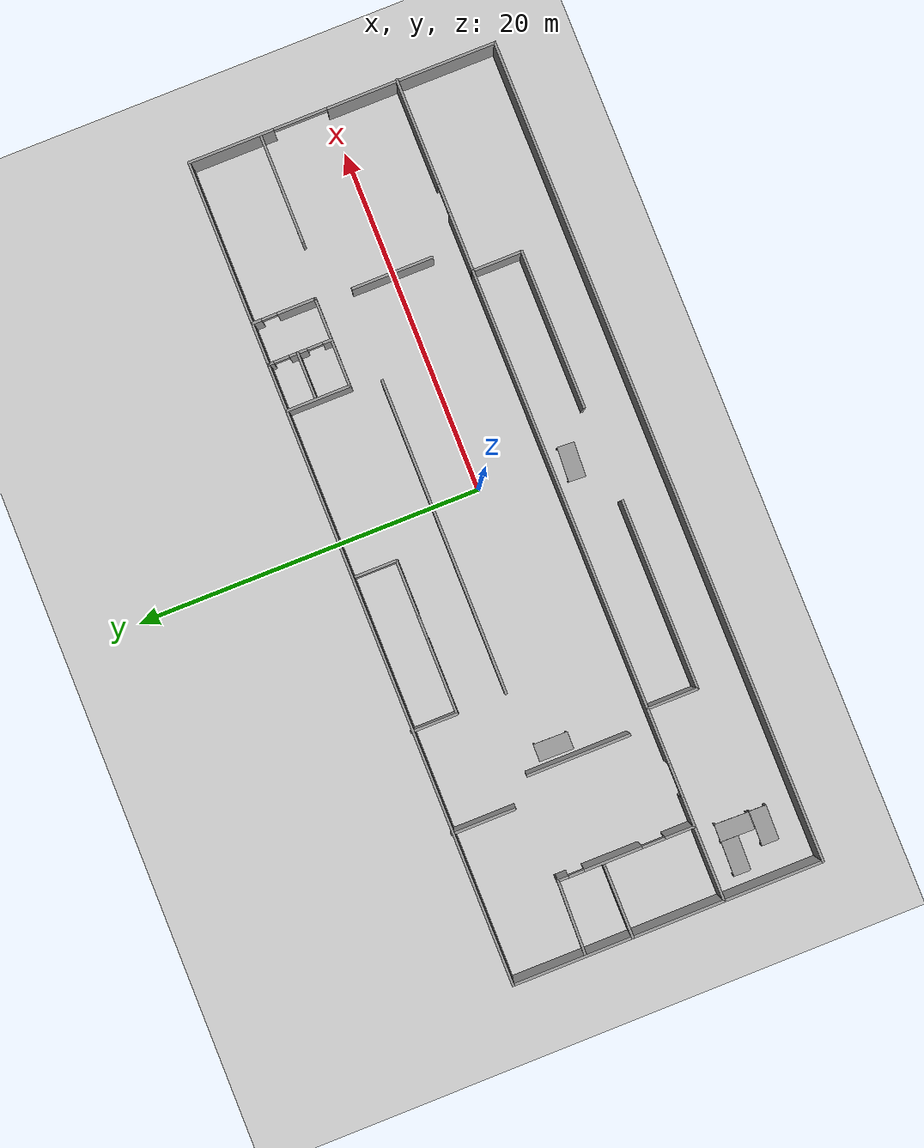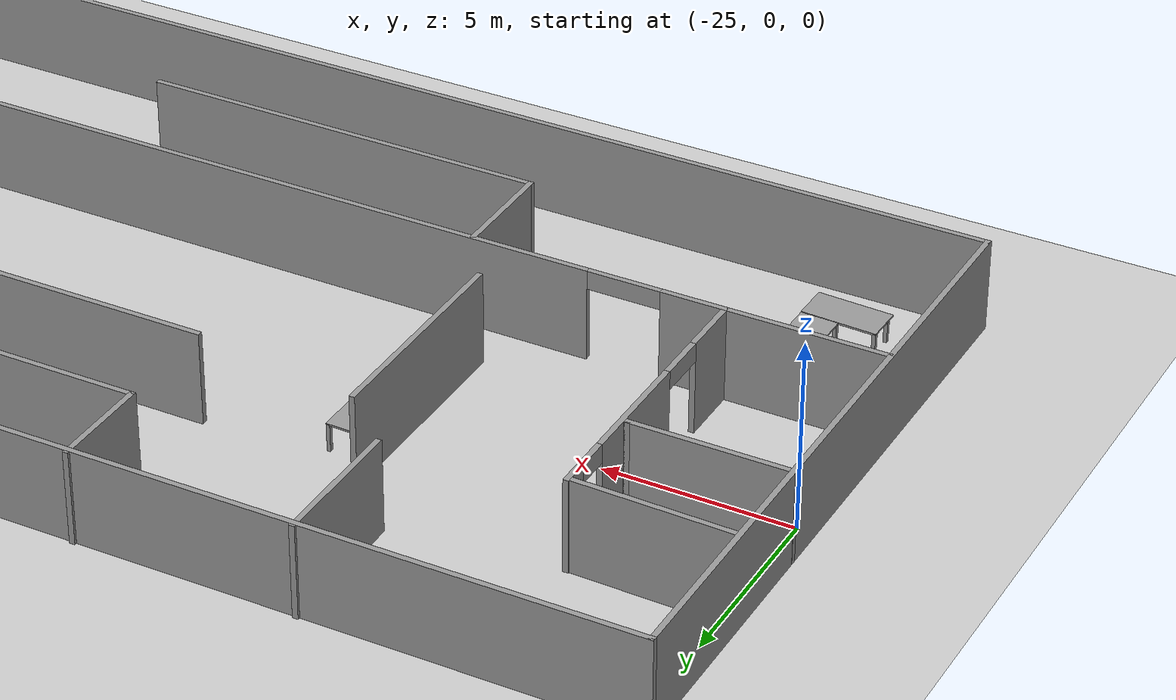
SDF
<sdf version="1.6">
 <world name="default">
  <light name="sun" type="directional">
   <pose>0 0 10 0 -0 0</pose>
   <diffuse>0.8 0.8 0.8 1</diffuse>
   <specular>0.2 0.2 0.2 1</specular>
   <attenuation>
    <range>1000</range>
    <constant>0.9</constant>
    <linear>0.01</linear>
    <quadratic>0.001</quadratic>
   </attenuation>
   <direction>-0.5 0.1 -0.9</direction>
  </light>
  <model name="ground_plane">
   <static>1</static>
   <link name="link">
    <collision name="collision">
     <geometry><plane><normal>0 0 1</normal><size>100 100</size></plane></geometry>
     <surface><friction><ode><mu>100</mu><mu2>50</mu2></ode></friction></surface>
    </collision>
    <visual name="visual">
     <cast_shadows>0</cast_shadows>
     <geometry><plane><normal>0 0 1</normal><size>100 100</size></plane></geometry>
     <material>
      <script><uri>file://media/materials/scripts/gazebo.material</uri><name>Gazebo/Grey</name></script>
     </material>
    </visual>
   </link>
  </model>
  <gravity>0 0 -9.8</gravity>
  <magnetic_field>6e-06 2.3e-05 -4.2e-05</magnetic_field>
  <atmosphere type="adiabatic"/>
  <physics name="default_physics" default="0" type="ode">
   <max_step_size>0.001</max_step_size>
   <real_time_factor>1</real_time_factor>
   <real_time_update_rate>1000</real_time_update_rate>
  </physics>
  <scene><ambient>0.4 0.4 0.4 1</ambient><background>0.7 0.7 0.7 1</background><shadows>1</shadows></scene>
  <spherical_coordinates>
   <surface_model>EARTH_WGS84</surface_model>
   <latitude_deg>0</latitude_deg>
   <longitude_deg>0</longitude_deg>
   <elevation>0</elevation>
   <heading_deg>0</heading_deg>
  </spherical_coordinates>
  <model name="spa">
   <pose>-1.5798 -0.751475 0 0 -0 0</pose>
   <link name="Wall_27">
    <collision name="Wall_27_Collision">
     <geometry><box><size>18 0.15 2.5</size></box></geometry>
     <pose>0 0 1.25 0 -0 0</pose>
    </collision>
    <visual name="Wall_27_Visual">
     <pose>0 0 1.25 0 -0 0</pose>
     <geometry><box><size>18 0.15 2.5</size></box></geometry>
     <material>
      <script><uri>file://media/materials/scripts/gazebo.material</uri><name>Gazebo/Grey</name></script>
      <ambient>1 1 1 1</ambient>
     </material>
     <meta><layer>0</layer></meta>
    </visual>
    <pose>-23.8238 -0.033638 0 0 0 -1.5708</pose>
   </link>
   <link name="Wall_28">
    <collision name="Wall_28_Collision">
     <geometry><box><size>47.75 0.15 2.5</size></box></geometry>
     <pose>0 0 1.25 0 -0 0</pose>
    </collision>
    <visual name="Wall_28_Visual">
     <pose>0 0 1.25 0 -0 0</pose>
     <geometry><box><size>47.75 0.15 2.5</size></box></geometry>
     <material>
      <script><uri>file://media/materials/scripts/gazebo.material</uri><name>Gazebo/Grey</name></script>
      <ambient>1 1 1 1</ambient>
     </material>
     <meta><layer>0</layer></meta>
    </visual>
    <pose>-0.023787 -8.95864 0 0 -0 0</pose>
   </link>
   <link name="Wall_29">
    <pose>23.7762 -0.033638 0 0 -0 1.5708</pose>
    <visual name="Wall_29_Visual_0">
     <pose>-4.06001 0 1.25 0 -0 0</pose>
     <geometry><box><size>9.87998 0.15 2.5</size></box></geometry>
     <material>
      <script><uri>file://media/materials/scripts/gazebo.material</uri><name>Gazebo/Grey</name></script>
      <ambient>1 1 1 1</ambient>
     </material>
     <meta><layer>0</layer></meta>
    </visual>
    <collision name="Wall_29_Collision_0">
     <geometry><box><size>9.87998 0.15 2.5</size></box></geometry>
     <pose>-4.06001 0 1.25 0 -0 0</pose>
    </collision>
    <visual name="Wall_29_Visual_1">
     <pose>6.49614 0 1.25 0 -0 0</pose>
     <geometry><box><size>5.00771 0.15 2.5</size></box></geometry>
     <material>
      <script><uri>file://media/materials/scripts/gazebo.material</uri><name>Gazebo/Grey</name></script>
      <ambient>1 1 1 1</ambient>
     </material>
     <meta><layer>0</layer></meta>
    </visual>
    <collision name="Wall_29_Collision_1">
     <geometry><box><size>5.00771 0.15 2.5</size></box></geometry>
     <pose>6.49614 0 1.25 0 -0 0</pose>
    </collision>
    <visual name="Wall_29_Visual_2">
     <pose>2.43613 0 2.25 0 -0 0</pose>
     <geometry><box><size>3.11231 0.15 0.5</size></box></geometry>
     <material>
      <script><uri>file://media/materials/scripts/gazebo.material</uri><name>Gazebo/Grey</name></script>
      <ambient>1 1 1 1</ambient>
     </material>
     <meta><layer>0</layer></meta>
    </visual>
    <collision name="Wall_29_Collision_2">
     <geometry><box><size>3.11231 0.15 0.5</size></box></geometry>
     <pose>2.43613 0 2.25 0 -0 0</pose>
    </collision>
   </link>
   <link name="Wall_30">
    <collision name="Wall_30_Collision">
     <geometry><box><size>47.75 0.15 2.5</size></box></geometry>
     <pose>0 0 1.25 0 -0 0</pose>
    </collision>
    <visual name="Wall_30_Visual">
     <pose>0 0 1.25 0 -0 0</pose>
     <geometry><box><size>47.75 0.15 2.5</size></box></geometry>
     <material>
      <script><uri>file://media/materials/scripts/gazebo.material</uri><name>Gazebo/Grey</name></script>
      <ambient>1 1 1 1</ambient>
     </material>
     <meta><layer>0</layer></meta>
    </visual>
    <pose>-0.023787 8.89136 0 0 -0 3.14159</pose>
   </link>
   <link name="Wall_32">
    <pose>0.0275 -3.25756 0 0 -0 3.14159</pose>
    <visual name="Wall_32_Visual_0">
     <pose>-20.77 0 1.25 0 -0 0</pose>
     <geometry><box><size>6.21002 0.15 2.5</size></box></geometry>
     <material>
      <script><uri>file://media/materials/scripts/gazebo.material</uri><name>Gazebo/Grey</name></script>
      <ambient>1 1 1 1</ambient>
     </material>
     <meta><layer>0</layer></meta>
    </visual>
    <collision name="Wall_32_Collision_0">
     <geometry><box><size>6.21002 0.15 2.5</size></box></geometry>
     <pose>-20.77 0 1.25 0 -0 0</pose>
    </collision>
    <visual name="Wall_32_Visual_1">
     <pose>-0.023773 0 1.25 0 -0 0</pose>
     <geometry><box><size>32.0075 0.15 2.5</size></box></geometry>
     <material>
      <script><uri>file://media/materials/scripts/gazebo.material</uri><name>Gazebo/Grey</name></script>
      <ambient>1 1 1 1</ambient>
     </material>
     <meta><layer>0</layer></meta>
    </visual>
    <collision name="Wall_32_Collision_1">
     <geometry><box><size>32.0075 0.15 2.5</size></box></geometry>
     <pose>-0.023773 0 1.25 0 -0 0</pose>
    </collision>
    <visual name="Wall_32_Visual_2">
     <pose>20.9006 0 1.25 0 -0 0</pose>
     <geometry><box><size>5.94875 0.15 2.5</size></box></geometry>
     <material>
      <script><uri>file://media/materials/scripts/gazebo.material</uri><name>Gazebo/Grey</name></script>
      <ambient>1 1 1 1</ambient>
     </material>
     <meta><layer>0</layer></meta>
    </visual>
    <collision name="Wall_32_Collision_2">
     <geometry><box><size>5.94875 0.15 2.5</size></box></geometry>
     <pose>20.9006 0 1.25 0 -0 0</pose>
    </collision>
    <visual name="Wall_32_Visual_3">
     <pose>-16.8463 0 2.25 0 -0 0</pose>
     <geometry><box><size>1.63744 0.15 0.5</size></box></geometry>
     <material>
      <script><uri>file://media/materials/scripts/gazebo.material</uri><name>Gazebo/Grey</name></script>
      <ambient>1 1 1 1</ambient>
     </material>
     <meta><layer>0</layer></meta>
    </visual>
    <collision name="Wall_32_Collision_3">
     <geometry><box><size>1.63744 0.15 0.5</size></box></geometry>
     <pose>-16.8463 0 2.25 0 -0 0</pose>
    </collision>
    <visual name="Wall_32_Visual_4">
     <pose>16.9531 0 2.25 0 -0 0</pose>
     <geometry><box><size>1.94625 0.15 0.5</size></box></geometry>
     <material>
      <script><uri>file://media/materials/scripts/gazebo.material</uri><name>Gazebo/Grey</name></script>
      <ambient>1 1 1 1</ambient>
     </material>
     <meta><layer>0</layer></meta>
    </visual>
    <collision name="Wall_32_Collision_4">
     <geometry><box><size>1.94625 0.15 0.5</size></box></geometry>
     <pose>16.9531 0 2.25 0 -0 0</pose>
    </collision>
   </link>
   <link name="Wall_34">
    <pose>-19.575 0.714943 0 0 0 -1.5708</pose>
    <visual name="Wall_34_Visual_0">
     <pose>-3.64471 0 1.25 0 -0 0</pose>
     <geometry><box><size>0.710585 0.15 2.5</size></box></geometry>
     <material>
      <script><uri>file://media/materials/scripts/gazebo.material</uri><name>Gazebo/Grey</name></script>
      <ambient>1 1 1 1</ambient>
     </material>
     <meta><layer>0</layer></meta>
    </visual>
    <collision name="Wall_34_Collision_0">
     <geometry><box><size>0.710585 0.15 2.5</size></box></geometry>
     <pose>-3.64471 0 1.25 0 -0 0</pose>
    </collision>
    <visual name="Wall_34_Visual_1">
     <pose>-0.719172 0 1.25 0 -0 0</pose>
     <geometry><box><size>3.34049 0.15 2.5</size></box></geometry>
     <material>
      <script><uri>file://media/materials/scripts/gazebo.material</uri><name>Gazebo/Grey</name></script>
      <ambient>1 1 1 1</ambient>
     </material>
     <meta><layer>0</layer></meta>
    </visual>
    <collision name="Wall_34_Collision_1">
     <geometry><box><size>3.34049 0.15 2.5</size></box></geometry>
     <pose>-0.719172 0 1.25 0 -0 0</pose>
    </collision>
    <visual name="Wall_34_Visual_2">
     <pose>3.14491 0 1.25 0 -0 0</pose>
     <geometry><box><size>1.71018 0.15 2.5</size></box></geometry>
     <material>
      <script><uri>file://media/materials/scripts/gazebo.material</uri><name>Gazebo/Grey</name></script>
      <ambient>1 1 1 1</ambient>
     </material>
     <meta><layer>0</layer></meta>
    </visual>
    <collision name="Wall_34_Collision_2">
     <geometry><box><size>1.71018 0.15 2.5</size></box></geometry>
     <pose>3.14491 0 1.25 0 -0 0</pose>
    </collision>
    <visual name="Wall_34_Visual_3">
     <pose>-2.83941 0 2.25 0 -0 0</pose>
     <geometry><box><size>0.9 0.15 0.5</size></box></geometry>
     <material>
      <script><uri>file://media/materials/scripts/gazebo.material</uri><name>Gazebo/Grey</name></script>
      <ambient>1 1 1 1</ambient>
     </material>
     <meta><layer>0</layer></meta>
    </visual>
    <collision name="Wall_34_Collision_3">
     <geometry><box><size>0.9 0.15 0.5</size></box></geometry>
     <pose>-2.83941 0 2.25 0 -0 0</pose>
    </collision>
    <visual name="Wall_34_Visual_4">
     <pose>1.62044 0 2.25 0 -0 0</pose>
     <geometry><box><size>1.33875 0.15 0.5</size></box></geometry>
     <material>
      <script><uri>file://media/materials/scripts/gazebo.material</uri><name>Gazebo/Grey</name></script>
      <ambient>1 1 1 1</ambient>
     </material>
     <meta><layer>0</layer></meta>
    </visual>
    <collision name="Wall_34_Collision_4">
     <geometry><box><size>1.33875 0.15 0.5</size></box></geometry>
     <pose>1.62044 0 2.25 0 -0 0</pose>
    </collision>
   </link>
   <link name="Wall_36">
    <collision name="Wall_36_Collision">
     <geometry><box><size>4.25056 0.15 2.5</size></box></geometry>
     <pose>0 0 1.25 0 -0 0</pose>
    </collision>
    <visual name="Wall_36_Visual">
     <pose>0 0 1.25 0 -0 0</pose>
     <geometry><box><size>4.25056 0.15 2.5</size></box></geometry>
     <material>
      <script><uri>file://media/materials/scripts/gazebo.material</uri><name>Gazebo/Grey</name></script>
      <ambient>1 1 1 1</ambient>
     </material>
     <meta><layer>0</layer></meta>
    </visual>
    <pose>-21.625 4.65682 0 0 -0 3.1169</pose>
   </link>
   <link name="Wall_38">
    <collision name="Wall_38_Collision">
     <geometry><box><size>4.25 0.15 2.5</size></box></geometry>
     <pose>0 0 1.25 0 -0 0</pose>
    </collision>
    <visual name="Wall_38_Visual">
     <pose>0 0 1.25 0 -0 0</pose>
     <geometry><box><size>4.25 0.15 2.5</size></box></geometry>
     <material>
      <script><uri>file://media/materials/scripts/gazebo.material</uri><name>Gazebo/Grey</name></script>
      <ambient>1 1 1 1</ambient>
     </material>
     <meta><layer>0</layer></meta>
    </visual>
    <pose>-21.7775 2.00744 0 0 -0 0</pose>
   </link>
   <link name="Wall_39">
    <collision name="Wall_39_Collision">
     <geometry><box><size>0.15 0.15 2.5</size></box></geometry>
     <pose>0 0 1.25 0 -0 0</pose>
    </collision>
    <visual name="Wall_39_Visual">
     <pose>0 0 1.25 0 -0 0</pose>
     <geometry><box><size>0.15 0.15 2.5</size></box></geometry>
     <material>
      <script><uri>file://media/materials/scripts/gazebo.material</uri><name>Gazebo/Grey</name></script>
      <ambient>1 1 1 1</ambient>
     </material>
     <meta><layer>0</layer></meta>
    </visual>
    <pose>-19.7275 2.00744 0 0 -0 0</pose>
   </link>
   <link name="Wall_41">
    <collision name="Wall_41_Collision">
     <geometry><box><size>3 0.15 2.5</size></box></geometry>
     <pose>0 0 1.25 0 -0 0</pose>
    </collision>
    <visual name="Wall_41_Visual">
     <pose>0 0 1.25 0 -0 0</pose>
     <geometry><box><size>3 0.15 2.5</size></box></geometry>
     <material>
      <script><uri>file://media/materials/scripts/gazebo.material</uri><name>Gazebo/Grey</name></script>
      <ambient>1 1 1 1</ambient>
     </material>
     <meta><layer>0</layer></meta>
    </visual>
    <pose>12.6225 -4.68256 0 0 0 -1.5708</pose>
   </link>
   <link name="Wall_42">
    <collision name="Wall_42_Collision">
     <geometry><box><size>9.25 0.15 2.5</size></box></geometry>
     <pose>0 0 1.25 0 -0 0</pose>
    </collision>
    <visual name="Wall_42_Visual">
     <pose>0 0 1.25 0 -0 0</pose>
     <geometry><box><size>9.25 0.15 2.5</size></box></geometry>
     <material>
      <script><uri>file://media/materials/scripts/gazebo.material</uri><name>Gazebo/Grey</name></script>
      <ambient>1 1 1 1</ambient>
     </material>
     <meta><layer>0</layer></meta>
    </visual>
    <pose>8.0725 -6.10756 0 0 -0 3.14159</pose>
   </link>
   <link name="Wall_44">
    <collision name="Wall_44_Collision">
     <geometry><box><size>11 0.15 2.5</size></box></geometry>
     <pose>0 0 1.25 0 -0 0</pose>
    </collision>
    <visual name="Wall_44_Visual">
     <pose>0 0 1.25 0 -0 0</pose>
     <geometry><box><size>11 0.15 2.5</size></box></geometry>
     <material>
      <script><uri>file://media/materials/scripts/gazebo.material</uri><name>Gazebo/Grey</name></script>
      <ambient>1 1 1 1</ambient>
     </material>
     <meta><layer>0</layer></meta>
    </visual>
    <pose>-7.3825 -6.16006 0 0 -0 3.14159</pose>
   </link>
   <link name="Wall_45">
    <collision name="Wall_45_Collision">
     <geometry><box><size>3 0.15 2.5</size></box></geometry>
     <pose>0 0 1.25 0 -0 0</pose>
    </collision>
    <visual name="Wall_45_Visual">
     <pose>0 0 1.25 0 -0 0</pose>
     <geometry><box><size>3 0.15 2.5</size></box></geometry>
     <material>
      <script><uri>file://media/materials/scripts/gazebo.material</uri><name>Gazebo/Grey</name></script>
      <ambient>1 1 1 1</ambient>
     </material>
     <meta><layer>0</layer></meta>
    </visual>
    <pose>-12.8075 -4.73506 0 0 -0 1.5708</pose>
   </link>
   <link name="Wall_47">
    <collision name="Wall_47_Collision">
     <geometry><box><size>6 0.15 2.5</size></box></geometry>
     <pose>0 0 1.25 0 -0 0</pose>
    </collision>
    <visual name="Wall_47_Visual">
     <pose>0 0 1.25 0 -0 0</pose>
     <geometry><box><size>6 0.15 2.5</size></box></geometry>
     <material>
      <script><uri>file://media/materials/scripts/gazebo.material</uri><name>Gazebo/Grey</name></script>
      <ambient>1 1 1 1</ambient>
     </material>
     <meta><layer>0</layer></meta>
    </visual>
    <pose>-13.7618 1.1032 0 0 0 -1.5708</pose>
   </link>
   <link name="Wall_49">
    <collision name="Wall_49_Collision">
     <geometry><box><size>3.75 0.15 2.5</size></box></geometry>
     <pose>0 0 1.25 0 -0 0</pose>
    </collision>
    <visual name="Wall_49_Visual">
     <pose>0 0 1.25 0 -0 0</pose>
     <geometry><box><size>3.75 0.15 2.5</size></box></geometry>
     <material>
      <script><uri>file://media/materials/scripts/gazebo.material</uri><name>Gazebo/Grey</name></script>
      <ambient>1 1 1 1</ambient>
     </material>
     <meta><layer>0</layer></meta>
    </visual>
    <pose>-15.1705 7.15864 0 0 0 -1.5708</pose>
   </link>
   <link name="Wall_51">
    <collision name="Wall_51_Collision">
     <geometry><box><size>18.25 0.15 2.5</size></box></geometry>
     <pose>0 0 1.25 0 -0 0</pose>
    </collision>
    <visual name="Wall_51_Visual">
     <pose>0 0 1.25 0 -0 0</pose>
     <geometry><box><size>18.25 0.15 2.5</size></box></geometry>
     <material>
      <script><uri>file://media/materials/scripts/gazebo.material</uri><name>Gazebo/Grey</name></script>
      <ambient>1 1 1 1</ambient>
     </material>
     <meta><layer>0</layer></meta>
    </visual>
    <pose>-0.192259 3.49994 0 0 -0 0</pose>
   </link>
   <link name="Wall_53">
    <collision name="Wall_53_Collision">
     <geometry><box><size>2.75 0.15 2.5</size></box></geometry>
     <pose>0 0 1.25 0 -0 0</pose>
    </collision>
    <visual name="Wall_53_Visual">
     <pose>0 0 1.25 0 -0 0</pose>
     <geometry><box><size>2.75 0.15 2.5</size></box></geometry>
     <material>
      <script><uri>file://media/materials/scripts/gazebo.material</uri><name>Gazebo/Grey</name></script>
      <ambient>1 1 1 1</ambient>
     </material>
     <meta><layer>0</layer></meta>
    </visual>
    <pose>-9.30096 7.65864 0 0 0 -1.5708</pose>
   </link>
   <link name="Wall_54">
    <pose>-4.87596 6.35864 0 0 -0 0</pose>
    <visual name="Wall_54_Visual_0">
     <pose>-2.29565 0 1.25 0 -0 0</pose>
     <geometry><box><size>4.4087 0.15 2.5</size></box></geometry>
     <material>
      <script><uri>file://media/materials/scripts/gazebo.material</uri><name>Gazebo/Grey</name></script>
      <ambient>1 1 1 1</ambient>
     </material>
     <meta><layer>0</layer></meta>
    </visual>
    <collision name="Wall_54_Collision_0">
     <geometry><box><size>4.4087 0.15 2.5</size></box></geometry>
     <pose>-2.29565 0 1.25 0 -0 0</pose>
    </collision>
    <visual name="Wall_54_Visual_1">
     <pose>2.85978 0 1.25 0 -0 0</pose>
     <geometry><box><size>3.28044 0.15 2.5</size></box></geometry>
     <material>
      <script><uri>file://media/materials/scripts/gazebo.material</uri><name>Gazebo/Grey</name></script>
      <ambient>1 1 1 1</ambient>
     </material>
     <meta><layer>0</layer></meta>
    </visual>
    <collision name="Wall_54_Collision_1">
     <geometry><box><size>3.28044 0.15 2.5</size></box></geometry>
     <pose>2.85978 0 1.25 0 -0 0</pose>
    </collision>
    <visual name="Wall_54_Visual_2">
     <pose>0.56413 0 2.25 0 -0 0</pose>
     <geometry><box><size>1.31087 0.15 0.5</size></box></geometry>
     <material>
      <script><uri>file://media/materials/scripts/gazebo.material</uri><name>Gazebo/Grey</name></script>
      <ambient>1 1 1 1</ambient>
     </material>
     <meta><layer>0</layer></meta>
    </visual>
    <collision name="Wall_54_Collision_2">
     <geometry><box><size>1.31087 0.15 0.5</size></box></geometry>
     <pose>0.56413 0 2.25 0 -0 0</pose>
    </collision>
   </link>
   <link name="Wall_55">
    <collision name="Wall_55_Collision">
     <geometry><box><size>2.5 0.15 2.5</size></box></geometry>
     <pose>0 0 1.25 0 -0 0</pose>
    </collision>
    <visual name="Wall_55_Visual">
     <pose>0 0 1.25 0 -0 0</pose>
     <geometry><box><size>2.5 0.15 2.5</size></box></geometry>
     <material>
      <script><uri>file://media/materials/scripts/gazebo.material</uri><name>Gazebo/Grey</name></script>
      <ambient>1 1 1 1</ambient>
     </material>
     <meta><layer>0</layer></meta>
    </visual>
    <pose>-0.450955 7.53364 0 0 -0 1.5708</pose>
   </link>
   <link name="Wall_57">
    <collision name="Wall_57_Collision">
     <geometry><box><size>3.75 0.15 2.5</size></box></geometry>
     <pose>0 0 1.25 0 -0 0</pose>
    </collision>
    <visual name="Wall_57_Visual">
     <pose>0 0 1.25 0 -0 0</pose>
     <geometry><box><size>3.75 0.15 2.5</size></box></geometry>
     <material>
      <script><uri>file://media/materials/scripts/gazebo.material</uri><name>Gazebo/Grey</name></script>
      <ambient>1 1 1 1</ambient>
     </material>
     <meta><layer>0</layer></meta>
    </visual>
    <pose>9.24687 7.04125 0 0 0 -1.5708</pose>
   </link>
   <link name="Wall_58">
    <collision name="Wall_58_Collision">
     <geometry><box><size>5.25 0.15 2.5</size></box></geometry>
     <pose>0 0 1.25 0 -0 0</pose>
    </collision>
    <visual name="Wall_58_Visual">
     <pose>0 0 1.25 0 -0 0</pose>
     <geometry><box><size>5.25 0.15 2.5</size></box></geometry>
     <material>
      <script><uri>file://media/materials/scripts/gazebo.material</uri><name>Gazebo/Grey</name></script>
      <ambient>1 1 1 1</ambient>
     </material>
     <meta><layer>0</layer></meta>
    </visual>
    <pose>11.7969 5.24125 0 0 -0 0</pose>
   </link>
   <link name="Wall_59">
    <pose>14.3469 7.04125 0 0 -0 1.5708</pose>
    <visual name="Wall_59_Visual_0">
     <pose>-0.732065 0 1.25 0 -0 0</pose>
     <geometry><box><size>2.28587 0.15 2.5</size></box></geometry>
     <material>
      <script><uri>file://media/materials/scripts/gazebo.material</uri><name>Gazebo/Grey</name></script>
      <ambient>1 1 1 1</ambient>
     </material>
     <meta><layer>0</layer></meta>
    </visual>
    <collision name="Wall_59_Collision_0">
     <geometry><box><size>2.28587 0.15 2.5</size></box></geometry>
     <pose>-0.732065 0 1.25 0 -0 0</pose>
    </collision>
    <visual name="Wall_59_Visual_1">
     <pose>1.59293 0 1.25 0 -0 0</pose>
     <geometry><box><size>0.56413 0.15 2.5</size></box></geometry>
     <material>
      <script><uri>file://media/materials/scripts/gazebo.material</uri><name>Gazebo/Grey</name></script>
      <ambient>1 1 1 1</ambient>
     </material>
     <meta><layer>0</layer></meta>
    </visual>
    <collision name="Wall_59_Collision_1">
     <geometry><box><size>0.56413 0.15 2.5</size></box></geometry>
     <pose>1.59293 0 1.25 0 -0 0</pose>
    </collision>
    <visual name="Wall_59_Visual_2">
     <pose>0.86087 0 2.25 0 -0 0</pose>
     <geometry><box><size>0.9 0.15 0.5</size></box></geometry>
     <material>
      <script><uri>file://media/materials/scripts/gazebo.material</uri><name>Gazebo/Grey</name></script>
      <ambient>1 1 1 1</ambient>
     </material>
     <meta><layer>0</layer></meta>
    </visual>
    <collision name="Wall_59_Collision_2">
     <geometry><box><size>0.9 0.15 0.5</size></box></geometry>
     <pose>0.86087 0 2.25 0 -0 0</pose>
    </collision>
   </link>
   <link name="Wall_61">
    <pose>11.9469 7.04125 0 0 0 -1.5708</pose>
    <visual name="Wall_61_Visual_0">
     <pose>-1.71033 0 1.25 0 -0 0</pose>
     <geometry><box><size>0.329347 0.15 2.5</size></box></geometry>
     <material>
      <script><uri>file://media/materials/scripts/gazebo.material</uri><name>Gazebo/Grey</name></script>
      <ambient>1 1 1 1</ambient>
     </material>
     <meta><layer>0</layer></meta>
    </visual>
    <collision name="Wall_61_Collision_0">
     <geometry><box><size>0.329347 0.15 2.5</size></box></geometry>
     <pose>-1.71033 0 1.25 0 -0 0</pose>
    </collision>
    <visual name="Wall_61_Visual_1">
     <pose>-0.127174 0 1.25 0 -0 0</pose>
     <geometry><box><size>1.03696 0.15 2.5</size></box></geometry>
     <material>
      <script><uri>file://media/materials/scripts/gazebo.material</uri><name>Gazebo/Grey</name></script>
      <ambient>1 1 1 1</ambient>
     </material>
     <meta><layer>0</layer></meta>
    </visual>
    <collision name="Wall_61_Collision_1">
     <geometry><box><size>1.03696 0.15 2.5</size></box></geometry>
     <pose>-0.127174 0 1.25 0 -0 0</pose>
    </collision>
    <visual name="Wall_61_Visual_2">
     <pose>1.58315 0 1.25 0 -0 0</pose>
     <geometry><box><size>0.583696 0.15 2.5</size></box></geometry>
     <material>
      <script><uri>file://media/materials/scripts/gazebo.material</uri><name>Gazebo/Grey</name></script>
      <ambient>1 1 1 1</ambient>
     </material>
     <meta><layer>0</layer></meta>
    </visual>
    <collision name="Wall_61_Collision_2">
     <geometry><box><size>0.583696 0.15 2.5</size></box></geometry>
     <pose>1.58315 0 1.25 0 -0 0</pose>
    </collision>
    <visual name="Wall_61_Visual_3">
     <pose>-1.09565 0 2.25 0 -0 0</pose>
     <geometry><box><size>0.9 0.15 0.5</size></box></geometry>
     <material>
      <script><uri>file://media/materials/scripts/gazebo.material</uri><name>Gazebo/Grey</name></script>
      <ambient>1 1 1 1</ambient>
     </material>
     <meta><layer>0</layer></meta>
    </visual>
    <collision name="Wall_61_Collision_3">
     <geometry><box><size>0.9 0.15 0.5</size></box></geometry>
     <pose>-1.09565 0 2.25 0 -0 0</pose>
    </collision>
    <visual name="Wall_61_Visual_4">
     <pose>0.841304 0 2.25 0 -0 0</pose>
     <geometry><box><size>0.9 0.15 0.5</size></box></geometry>
     <material>
      <script><uri>file://media/materials/scripts/gazebo.material</uri><name>Gazebo/Grey</name></script>
      <ambient>1 1 1 1</ambient>
     </material>
     <meta><layer>0</layer></meta>
    </visual>
    <collision name="Wall_61_Collision_4">
     <geometry><box><size>0.9 0.15 0.5</size></box></geometry>
     <pose>0.841304 0 2.25 0 -0 0</pose>
    </collision>
   </link>
   <link name="Wall_63">
    <collision name="Wall_63_Collision">
     <geometry><box><size>2.75 0.15 2.5</size></box></geometry>
     <pose>0 0 1.25 0 -0 0</pose>
    </collision>
    <visual name="Wall_63_Visual">
     <pose>0 0 1.25 0 -0 0</pose>
     <geometry><box><size>2.75 0.15 2.5</size></box></geometry>
     <material>
      <script><uri>file://media/materials/scripts/gazebo.material</uri><name>Gazebo/Grey</name></script>
      <ambient>1 1 1 1</ambient>
     </material>
     <meta><layer>0</layer></meta>
    </visual>
    <pose>10.6469 7.19777 0 0 -0 3.14159</pose>
   </link>
   <link name="Wall_65">
    <collision name="Wall_65_Collision">
     <geometry><box><size>6.25 0.15 2.5</size></box></geometry>
     <pose>0 0 1.25 0 -0 0</pose>
    </collision>
    <visual name="Wall_65_Visual">
     <pose>0 0 1.25 0 -0 0</pose>
     <geometry><box><size>6.25 0.15 2.5</size></box></geometry>
     <material>
      <script><uri>file://media/materials/scripts/gazebo.material</uri><name>Gazebo/Grey</name></script>
      <ambient>1 1 1 1</ambient>
     </material>
     <meta><layer>0</layer></meta>
    </visual>
    <pose>20.5773 4.73255 0 0 -0 3.14159</pose>
   </link>
   <link name="Wall_67">
    <collision name="Wall_67_Collision">
     <geometry><box><size>4.75 0.15 2.5</size></box></geometry>
     <pose>0 0 1.25 0 -0 0</pose>
    </collision>
    <visual name="Wall_67_Visual">
     <pose>0 0 1.25 0 -0 0</pose>
     <geometry><box><size>4.75 0.15 2.5</size></box></geometry>
     <material>
      <script><uri>file://media/materials/scripts/gazebo.material</uri><name>Gazebo/Grey</name></script>
      <ambient>1 1 1 1</ambient>
     </material>
     <meta><layer>0</layer></meta>
    </visual>
    <pose>14.1186 0.847769 0 0 0 -1.5708</pose>
   </link>
   <static>1</static>
  </model>
  <model name="table">
   <link name="link_2">
    <pose>-0.000914 0.01077 -0.287764 0 -0 0</pose>
    <inertial>
     <mass>1</mass>
     <inertia>
      <ixx>0.166667</ixx>
      <ixy>0</ixy>
      <ixz>0</ixz>
      <iyy>0.166667</iyy>
      <iyz>0</iyz>
      <izz>0.166667</izz>
     </inertia>
    </inertial>
    <visual name="visual">
     <pose>0 0 0.75 0 -0 0</pose>
     <geometry><box><size>1 2 0.05</size></box></geometry>
     <material>
      <lighting>1</lighting>
      <script><uri>file://media/materials/scripts/gazebo.material</uri><name>Gazebo/Grey</name></script>
      <ambient>0.3 0.3 0.3 1</ambient>
      <diffuse>0.7 0.7 0.7 1</diffuse>
      <specular>0.01 0.01 0.01 1</specular>
      <emissive>0 0 0 1</emissive>
      <shader type="vertex"><normal_map>__default__</normal_map></shader>
     </material>
    </visual>
    <collision name="collision">
     <pose>0 0 0.75 0 -0 0</pose>
     <geometry><box><size>1 2 0.05</size></box></geometry>
     <surface>
      <friction>
       <ode><mu>1</mu><mu2>1</mu2><fdir1>0 0 0</fdir1><slip1>0</slip1><slip2>0</slip2></ode>
       <torsional>
        <coefficient>1</coefficient>
        <patch_radius>0</patch_radius>
        <surface_radius>0</surface_radius>
        <use_patch_radius>1</use_patch_radius>
        <ode><slip>0</slip></ode>
       </torsional>
      </friction>
      <bounce><restitution_coefficient>0</restitution_coefficient><threshold>1e+06</threshold></bounce>
      <contact>
       <collide_without_contact>0</collide_without_contact>
       <collide_without_contact_bitmask>1</collide_without_contact_bitmask>
       <collide_bitmask>1</collide_bitmask>
       <ode>
        <soft_cfm>0</soft_cfm>
        <soft_erp>0.2</soft_erp>
        <kp>1e+13</kp>
        <kd>1</kd>
        <max_vel>0.01</max_vel>
        <min_depth>0</min_depth>
       </ode>
       <bullet>
        <split_impulse>1</split_impulse>
        <split_impulse_penetration_threshold>-0.01</split_impulse_penetration_threshold>
        <soft_cfm>0</soft_cfm>
        <soft_erp>0.2</soft_erp>
        <kp>1e+13</kp>
        <kd>1</kd>
       </bullet>
      </contact>
     </surface>
    </collision>
   </link>
   <link name="link_3">
    <pose>-0.450914 0.87078 0.080236 0 -0 0</pose>
    <inertial>
     <mass>1</mass>
     <inertia>
      <ixx>0.166667</ixx>
      <ixy>0</ixy>
      <ixz>0</ixz>
      <iyy>0.166667</iyy>
      <iyz>0</iyz>
      <izz>0.166667</izz>
     </inertia>
    </inertial>
    <visual name="visual">
     <geometry><box><size>0.1 0.1 0.75</size></box></geometry>
     <material>
      <lighting>1</lighting>
      <script><uri>file://media/materials/scripts/gazebo.material</uri><name>Gazebo/Grey</name></script>
      <ambient>0.3 0.3 0.3 1</ambient>
      <diffuse>0.7 0.7 0.7 1</diffuse>
      <specular>0.01 0.01 0.01 1</specular>
      <emissive>0 0 0 1</emissive>
      <shader type="vertex"><normal_map>__default__</normal_map></shader>
     </material>
    </visual>
    <collision name="collision">
     <geometry><box><size>0.1 0.1 0.75</size></box></geometry>
     <surface>
      <friction>
       <ode><mu>1</mu><mu2>1</mu2><fdir1>0 0 0</fdir1><slip1>0</slip1><slip2>0</slip2></ode>
       <torsional>
        <coefficient>1</coefficient>
        <patch_radius>0</patch_radius>
        <surface_radius>0</surface_radius>
        <use_patch_radius>1</use_patch_radius>
        <ode><slip>0</slip></ode>
       </torsional>
      </friction>
      <bounce><restitution_coefficient>0</restitution_coefficient><threshold>1e+06</threshold></bounce>
      <contact>
       <collide_without_contact>0</collide_without_contact>
       <collide_without_contact_bitmask>1</collide_without_contact_bitmask>
       <collide_bitmask>1</collide_bitmask>
       <ode>
        <soft_cfm>0</soft_cfm>
        <soft_erp>0.2</soft_erp>
        <kp>1e+13</kp>
        <kd>1</kd>
        <max_vel>0.01</max_vel>
        <min_depth>0</min_depth>
       </ode>
       <bullet>
        <split_impulse>1</split_impulse>
        <split_impulse_penetration_threshold>-0.01</split_impulse_penetration_threshold>
        <soft_cfm>0</soft_cfm>
        <soft_erp>0.2</soft_erp>
        <kp>1e+13</kp>
        <kd>1</kd>
       </bullet>
      </contact>
     </surface>
    </collision>
   </link>
   <link name="link_3_clone_0">
    <pose>0.45366 -0.903088 0.047057 0 -0 0</pose>
    <inertial>
     <mass>1</mass>
     <inertia>
      <ixx>0.166667</ixx>
      <ixy>0</ixy>
      <ixz>0</ixz>
      <iyy>0.166667</iyy>
      <iyz>0</iyz>
      <izz>0.166667</izz>
     </inertia>
    </inertial>
    <visual name="visual">
     <geometry><box><size>0.1 0.1 0.75</size></box></geometry>
     <material>
      <lighting>1</lighting>
      <script><uri>file://media/materials/scripts/gazebo.material</uri><name>Gazebo/Grey</name></script>
      <ambient>0.3 0.3 0.3 1</ambient>
      <diffuse>0.7 0.7 0.7 1</diffuse>
      <specular>0.01 0.01 0.01 1</specular>
      <emissive>0 0 0 1</emissive>
      <shader type="vertex"><normal_map>__default__</normal_map></shader>
     </material>
    </visual>
    <collision name="collision">
     <geometry><box><size>0.1 0.1 0.75</size></box></geometry>
     <surface>
      <friction>
       <ode><mu>1</mu><mu2>1</mu2><fdir1>0 0 0</fdir1><slip1>0</slip1><slip2>0</slip2></ode>
       <torsional>
        <coefficient>1</coefficient>
        <patch_radius>0</patch_radius>
        <surface_radius>0</surface_radius>
        <use_patch_radius>1</use_patch_radius>
        <ode><slip>0</slip></ode>
       </torsional>
      </friction>
      <bounce><restitution_coefficient>0</restitution_coefficient><threshold>1e+06</threshold></bounce>
      <contact>
       <collide_without_contact>0</collide_without_contact>
       <collide_without_contact_bitmask>1</collide_without_contact_bitmask>
       <collide_bitmask>1</collide_bitmask>
       <ode>
        <soft_cfm>0</soft_cfm>
        <soft_erp>0.2</soft_erp>
        <kp>1e+13</kp>
        <kd>1</kd>
        <max_vel>0.01</max_vel>
        <min_depth>0</min_depth>
       </ode>
       <bullet>
        <split_impulse>1</split_impulse>
        <split_impulse_penetration_threshold>-0.01</split_impulse_penetration_threshold>
        <soft_cfm>0</soft_cfm>
        <soft_erp>0.2</soft_erp>
        <kp>1e+13</kp>
        <kd>1</kd>
       </bullet>
      </contact>
     </surface>
    </collision>
   </link>
   <link name="link_3_clone_0_clone">
    <pose>-0.450914 -0.93923 0.080236 -0.02 0 0</pose>
    <inertial>
     <mass>1</mass>
     <inertia>
      <ixx>0.166667</ixx>
      <ixy>0</ixy>
      <ixz>0</ixz>
      <iyy>0.166667</iyy>
      <iyz>0</iyz>
      <izz>0.166667</izz>
     </inertia>
    </inertial>
    <visual name="visual">
     <geometry><box><size>0.1 0.1 0.75</size></box></geometry>
     <material>
      <lighting>1</lighting>
      <script><uri>file://media/materials/scripts/gazebo.material</uri><name>Gazebo/Grey</name></script>
      <ambient>0.3 0.3 0.3 1</ambient>
      <diffuse>0.7 0.7 0.7 1</diffuse>
      <specular>0.01 0.01 0.01 1</specular>
      <emissive>0 0 0 1</emissive>
      <shader type="vertex"><normal_map>__default__</normal_map></shader>
     </material>
    </visual>
    <collision name="collision">
     <geometry><box><size>0.1 0.1 0.75</size></box></geometry>
     <surface>
      <friction>
       <ode><mu>1</mu><mu2>1</mu2><fdir1>0 0 0</fdir1><slip1>0</slip1><slip2>0</slip2></ode>
       <torsional>
        <coefficient>1</coefficient>
        <patch_radius>0</patch_radius>
        <surface_radius>0</surface_radius>
        <use_patch_radius>1</use_patch_radius>
        <ode><slip>0</slip></ode>
       </torsional>
      </friction>
      <bounce><restitution_coefficient>0</restitution_coefficient><threshold>1e+06</threshold></bounce>
      <contact>
       <collide_without_contact>0</collide_without_contact>
       <collide_without_contact_bitmask>1</collide_without_contact_bitmask>
       <collide_bitmask>1</collide_bitmask>
       <ode>
        <soft_cfm>0</soft_cfm>
        <soft_erp>0.2</soft_erp>
        <kp>1e+13</kp>
        <kd>1</kd>
        <max_vel>0.01</max_vel>
        <min_depth>0</min_depth>
       </ode>
       <bullet>
        <split_impulse>1</split_impulse>
        <split_impulse_penetration_threshold>-0.01</split_impulse_penetration_threshold>
        <soft_cfm>0</soft_cfm>
        <soft_erp>0.2</soft_erp>
        <kp>1e+13</kp>
        <kd>1</kd>
       </bullet>
      </contact>
     </surface>
    </collision>
   </link>
   <link name="link_3_clone_1">
    <pose>0.449089 0.960775 0.080236 0 -0 0</pose>
    <inertial>
     <mass>1</mass>
     <inertia>
      <ixx>0.166667</ixx>
      <ixy>0</ixy>
      <ixz>0</ixz>
      <iyy>0.166667</iyy>
      <iyz>0</iyz>
      <izz>0.166667</izz>
     </inertia>
    </inertial>
    <visual name="visual">
     <geometry><box><size>0.1 0.1 0.75</size></box></geometry>
     <material>
      <lighting>1</lighting>
      <script><uri>file://media/materials/scripts/gazebo.material</uri><name>Gazebo/Grey</name></script>
      <ambient>0.3 0.3 0.3 1</ambient>
      <diffuse>0.7 0.7 0.7 1</diffuse>
      <specular>0.01 0.01 0.01 1</specular>
      <emissive>0 0 0 1</emissive>
      <shader type="vertex"><normal_map>__default__</normal_map></shader>
     </material>
    </visual>
    <collision name="collision">
     <geometry><box><size>0.1 0.1 0.75</size></box></geometry>
     <surface>
      <friction>
       <ode><mu>1</mu><mu2>1</mu2><fdir1>0 0 0</fdir1><slip1>0</slip1><slip2>0</slip2></ode>
       <torsional>
        <coefficient>1</coefficient>
        <patch_radius>0</patch_radius>
        <surface_radius>0</surface_radius>
        <use_patch_radius>1</use_patch_radius>
        <ode><slip>0</slip></ode>
       </torsional>
      </friction>
      <bounce><restitution_coefficient>0</restitution_coefficient><threshold>1e+06</threshold></bounce>
      <contact>
       <collide_without_contact>0</collide_without_contact>
       <collide_without_contact_bitmask>1</collide_without_contact_bitmask>
       <collide_bitmask>1</collide_bitmask>
       <ode>
        <soft_cfm>0</soft_cfm>
        <soft_erp>0.2</soft_erp>
        <kp>1e+13</kp>
        <kd>1</kd>
        <max_vel>0.01</max_vel>
        <min_depth>0</min_depth>
       </ode>
       <bullet>
        <split_impulse>1</split_impulse>
        <split_impulse_penetration_threshold>-0.01</split_impulse_penetration_threshold>
        <soft_cfm>0</soft_cfm>
        <soft_erp>0.2</soft_erp>
        <kp>1e+13</kp>
        <kd>1</kd>
       </bullet>
      </contact>
     </surface>
    </collision>
   </link>
   <joint name="link_2_JOINT_10" type="fixed">
    <parent>link_2</parent>
    <child>link_3_clone_1</child>
    <physics>
     <ode><limit><cfm>0</cfm><erp>0.2</erp></limit><suspension><cfm>0</cfm><erp>0.2</erp></suspension></ode>
    </physics>
   </joint>
   <joint name="link_2_JOINT_11" type="fixed">
    <parent>link_2</parent>
    <child>link_3</child>
    <physics>
     <ode><limit><cfm>0</cfm><erp>0.2</erp></limit><suspension><cfm>0</cfm><erp>0.2</erp></suspension></ode>
    </physics>
   </joint>
   <joint name="link_2_JOINT_12" type="fixed">
    <parent>link_2</parent>
    <child>link_3_clone_0_clone</child>
    <physics>
     <ode><limit><cfm>0</cfm><erp>0.2</erp></limit><suspension><cfm>0</cfm><erp>0.2</erp></suspension></ode>
    </physics>
   </joint>
   <joint name="link_2_JOINT_8" type="fixed">
    <parent>link_2</parent>
    <child>link_3_clone_0</child>
    <physics>
     <ode><limit><cfm>0</cfm><erp>0.2</erp></limit><suspension><cfm>0</cfm><erp>0.2</erp></suspension></ode>
    </physics>
   </joint>
   <joint name="link_2_JOINT_9" type="fixed">
    <parent>link_2</parent>
    <child>link_3</child>
    <physics>
     <ode><limit><cfm>0</cfm><erp>0.2</erp></limit><suspension><cfm>0</cfm><erp>0.2</erp></suspension></ode>
    </physics>
   </joint>
   <static>0</static>
   <pose>-14.5412 1.38149 0.311988 -0.01779 -0.001786 -0.013764</pose>
  </model>
  <model name="table_0">
   <link name="link_2">
    <pose>-0.000914 0.01077 -0.287764 0 -0 0</pose>
    <inertial>
     <mass>1</mass>
     <inertia>
      <ixx>0.166667</ixx>
      <ixy>0</ixy>
      <ixz>0</ixz>
      <iyy>0.166667</iyy>
      <iyz>0</iyz>
      <izz>0.166667</izz>
     </inertia>
    </inertial>
    <visual name="visual">
     <pose>0 0 0.75 0 -0 0</pose>
     <geometry><box><size>1 2 0.05</size></box></geometry>
     <material>
      <lighting>1</lighting>
      <script><uri>file://media/materials/scripts/gazebo.material</uri><name>Gazebo/Grey</name></script>
      <ambient>0.3 0.3 0.3 1</ambient>
      <diffuse>0.7 0.7 0.7 1</diffuse>
      <specular>0.01 0.01 0.01 1</specular>
      <emissive>0 0 0 1</emissive>
      <shader type="vertex"><normal_map>__default__</normal_map></shader>
     </material>
    </visual>
    <collision name="collision">
     <pose>0 0 0.75 0 -0 0</pose>
     <geometry><box><size>1 2 0.05</size></box></geometry>
     <surface>
      <friction>
       <ode><mu>1</mu><mu2>1</mu2><fdir1>0 0 0</fdir1><slip1>0</slip1><slip2>0</slip2></ode>
       <torsional>
        <coefficient>1</coefficient>
        <patch_radius>0</patch_radius>
        <surface_radius>0</surface_radius>
        <use_patch_radius>1</use_patch_radius>
        <ode><slip>0</slip></ode>
       </torsional>
      </friction>
      <bounce><restitution_coefficient>0</restitution_coefficient><threshold>1e+06</threshold></bounce>
      <contact>
       <collide_without_contact>0</collide_without_contact>
       <collide_without_contact_bitmask>1</collide_without_contact_bitmask>
       <collide_bitmask>1</collide_bitmask>
       <ode>
        <soft_cfm>0</soft_cfm>
        <soft_erp>0.2</soft_erp>
        <kp>1e+13</kp>
        <kd>1</kd>
        <max_vel>0.01</max_vel>
        <min_depth>0</min_depth>
       </ode>
       <bullet>
        <split_impulse>1</split_impulse>
        <split_impulse_penetration_threshold>-0.01</split_impulse_penetration_threshold>
        <soft_cfm>0</soft_cfm>
        <soft_erp>0.2</soft_erp>
        <kp>1e+13</kp>
        <kd>1</kd>
       </bullet>
      </contact>
     </surface>
    </collision>
   </link>
   <link name="link_3">
    <pose>-0.450914 0.87078 0.080236 0 -0 0</pose>
    <inertial>
     <mass>1</mass>
     <inertia>
      <ixx>0.166667</ixx>
      <ixy>0</ixy>
      <ixz>0</ixz>
      <iyy>0.166667</iyy>
      <iyz>0</iyz>
      <izz>0.166667</izz>
     </inertia>
    </inertial>
    <visual name="visual">
     <geometry><box><size>0.1 0.1 0.75</size></box></geometry>
     <material>
      <lighting>1</lighting>
      <script><uri>file://media/materials/scripts/gazebo.material</uri><name>Gazebo/Grey</name></script>
      <ambient>0.3 0.3 0.3 1</ambient>
      <diffuse>0.7 0.7 0.7 1</diffuse>
      <specular>0.01 0.01 0.01 1</specular>
      <emissive>0 0 0 1</emissive>
      <shader type="vertex"><normal_map>__default__</normal_map></shader>
     </material>
    </visual>
    <collision name="collision">
     <geometry><box><size>0.1 0.1 0.75</size></box></geometry>
     <surface>
      <friction>
       <ode><mu>1</mu><mu2>1</mu2><fdir1>0 0 0</fdir1><slip1>0</slip1><slip2>0</slip2></ode>
       <torsional>
        <coefficient>1</coefficient>
        <patch_radius>0</patch_radius>
        <surface_radius>0</surface_radius>
        <use_patch_radius>1</use_patch_radius>
        <ode><slip>0</slip></ode>
       </torsional>
      </friction>
      <bounce><restitution_coefficient>0</restitution_coefficient><threshold>1e+06</threshold></bounce>
      <contact>
       <collide_without_contact>0</collide_without_contact>
       <collide_without_contact_bitmask>1</collide_without_contact_bitmask>
       <collide_bitmask>1</collide_bitmask>
       <ode>
        <soft_cfm>0</soft_cfm>
        <soft_erp>0.2</soft_erp>
        <kp>1e+13</kp>
        <kd>1</kd>
        <max_vel>0.01</max_vel>
        <min_depth>0</min_depth>
       </ode>
       <bullet>
        <split_impulse>1</split_impulse>
        <split_impulse_penetration_threshold>-0.01</split_impulse_penetration_threshold>
        <soft_cfm>0</soft_cfm>
        <soft_erp>0.2</soft_erp>
        <kp>1e+13</kp>
        <kd>1</kd>
       </bullet>
      </contact>
     </surface>
    </collision>
   </link>
   <link name="link_3_clone_0">
    <pose>0.45366 -0.903088 0.047057 0 -0 0</pose>
    <inertial>
     <mass>1</mass>
     <inertia>
      <ixx>0.166667</ixx>
      <ixy>0</ixy>
      <ixz>0</ixz>
      <iyy>0.166667</iyy>
      <iyz>0</iyz>
      <izz>0.166667</izz>
     </inertia>
    </inertial>
    <visual name="visual">
     <geometry><box><size>0.1 0.1 0.75</size></box></geometry>
     <material>
      <lighting>1</lighting>
      <script><uri>file://media/materials/scripts/gazebo.material</uri><name>Gazebo/Grey</name></script>
      <ambient>0.3 0.3 0.3 1</ambient>
      <diffuse>0.7 0.7 0.7 1</diffuse>
      <specular>0.01 0.01 0.01 1</specular>
      <emissive>0 0 0 1</emissive>
      <shader type="vertex"><normal_map>__default__</normal_map></shader>
     </material>
    </visual>
    <collision name="collision">
     <geometry><box><size>0.1 0.1 0.75</size></box></geometry>
     <surface>
      <friction>
       <ode><mu>1</mu><mu2>1</mu2><fdir1>0 0 0</fdir1><slip1>0</slip1><slip2>0</slip2></ode>
       <torsional>
        <coefficient>1</coefficient>
        <patch_radius>0</patch_radius>
        <surface_radius>0</surface_radius>
        <use_patch_radius>1</use_patch_radius>
        <ode><slip>0</slip></ode>
       </torsional>
      </friction>
      <bounce><restitution_coefficient>0</restitution_coefficient><threshold>1e+06</threshold></bounce>
      <contact>
       <collide_without_contact>0</collide_without_contact>
       <collide_without_contact_bitmask>1</collide_without_contact_bitmask>
       <collide_bitmask>1</collide_bitmask>
       <ode>
        <soft_cfm>0</soft_cfm>
        <soft_erp>0.2</soft_erp>
        <kp>1e+13</kp>
        <kd>1</kd>
        <max_vel>0.01</max_vel>
        <min_depth>0</min_depth>
       </ode>
       <bullet>
        <split_impulse>1</split_impulse>
        <split_impulse_penetration_threshold>-0.01</split_impulse_penetration_threshold>
        <soft_cfm>0</soft_cfm>
        <soft_erp>0.2</soft_erp>
        <kp>1e+13</kp>
        <kd>1</kd>
       </bullet>
      </contact>
     </surface>
    </collision>
   </link>
   <link name="link_3_clone_0_clone">
    <pose>-0.450914 -0.93923 0.080236 -0.02 0 0</pose>
    <inertial>
     <mass>1</mass>
     <inertia>
      <ixx>0.166667</ixx>
      <ixy>0</ixy>
      <ixz>0</ixz>
      <iyy>0.166667</iyy>
      <iyz>0</iyz>
      <izz>0.166667</izz>
     </inertia>
    </inertial>
    <visual name="visual">
     <geometry><box><size>0.1 0.1 0.75</size></box></geometry>
     <material>
      <lighting>1</lighting>
      <script><uri>file://media/materials/scripts/gazebo.material</uri><name>Gazebo/Grey</name></script>
      <ambient>0.3 0.3 0.3 1</ambient>
      <diffuse>0.7 0.7 0.7 1</diffuse>
      <specular>0.01 0.01 0.01 1</specular>
      <emissive>0 0 0 1</emissive>
      <shader type="vertex"><normal_map>__default__</normal_map></shader>
     </material>
    </visual>
    <collision name="collision">
     <geometry><box><size>0.1 0.1 0.75</size></box></geometry>
     <surface>
      <friction>
       <ode><mu>1</mu><mu2>1</mu2><fdir1>0 0 0</fdir1><slip1>0</slip1><slip2>0</slip2></ode>
       <torsional>
        <coefficient>1</coefficient>
        <patch_radius>0</patch_radius>
        <surface_radius>0</surface_radius>
        <use_patch_radius>1</use_patch_radius>
        <ode><slip>0</slip></ode>
       </torsional>
      </friction>
      <bounce><restitution_coefficient>0</restitution_coefficient><threshold>1e+06</threshold></bounce>
      <contact>
       <collide_without_contact>0</collide_without_contact>
       <collide_without_contact_bitmask>1</collide_without_contact_bitmask>
       <collide_bitmask>1</collide_bitmask>
       <ode>
        <soft_cfm>0</soft_cfm>
        <soft_erp>0.2</soft_erp>
        <kp>1e+13</kp>
        <kd>1</kd>
        <max_vel>0.01</max_vel>
        <min_depth>0</min_depth>
       </ode>
       <bullet>
        <split_impulse>1</split_impulse>
        <split_impulse_penetration_threshold>-0.01</split_impulse_penetration_threshold>
        <soft_cfm>0</soft_cfm>
        <soft_erp>0.2</soft_erp>
        <kp>1e+13</kp>
        <kd>1</kd>
       </bullet>
      </contact>
     </surface>
    </collision>
   </link>
   <link name="link_3_clone_1">
    <pose>0.449089 0.960775 0.080236 0 -0 0</pose>
    <inertial>
     <mass>1</mass>
     <inertia>
      <ixx>0.166667</ixx>
      <ixy>0</ixy>
      <ixz>0</ixz>
      <iyy>0.166667</iyy>
      <iyz>0</iyz>
      <izz>0.166667</izz>
     </inertia>
    </inertial>
    <visual name="visual">
     <geometry><box><size>0.1 0.1 0.75</size></box></geometry>
     <material>
      <lighting>1</lighting>
      <script><uri>file://media/materials/scripts/gazebo.material</uri><name>Gazebo/Grey</name></script>
      <ambient>0.3 0.3 0.3 1</ambient>
      <diffuse>0.7 0.7 0.7 1</diffuse>
      <specular>0.01 0.01 0.01 1</specular>
      <emissive>0 0 0 1</emissive>
      <shader type="vertex"><normal_map>__default__</normal_map></shader>
     </material>
    </visual>
    <collision name="collision">
     <geometry><box><size>0.1 0.1 0.75</size></box></geometry>
     <surface>
      <friction>
       <ode><mu>1</mu><mu2>1</mu2><fdir1>0 0 0</fdir1><slip1>0</slip1><slip2>0</slip2></ode>
       <torsional>
        <coefficient>1</coefficient>
        <patch_radius>0</patch_radius>
        <surface_radius>0</surface_radius>
        <use_patch_radius>1</use_patch_radius>
        <ode><slip>0</slip></ode>
       </torsional>
      </friction>
      <bounce><restitution_coefficient>0</restitution_coefficient><threshold>1e+06</threshold></bounce>
      <contact>
       <collide_without_contact>0</collide_without_contact>
       <collide_without_contact_bitmask>1</collide_without_contact_bitmask>
       <collide_bitmask>1</collide_bitmask>
       <ode>
        <soft_cfm>0</soft_cfm>
        <soft_erp>0.2</soft_erp>
        <kp>1e+13</kp>
        <kd>1</kd>
        <max_vel>0.01</max_vel>
        <min_depth>0</min_depth>
       </ode>
       <bullet>
        <split_impulse>1</split_impulse>
        <split_impulse_penetration_threshold>-0.01</split_impulse_penetration_threshold>
        <soft_cfm>0</soft_cfm>
        <soft_erp>0.2</soft_erp>
        <kp>1e+13</kp>
        <kd>1</kd>
       </bullet>
      </contact>
     </surface>
    </collision>
   </link>
   <joint name="link_2_JOINT_10" type="fixed">
    <parent>link_2</parent>
    <child>link_3_clone_1</child>
    <physics>
     <ode><limit><cfm>0</cfm><erp>0.2</erp></limit><suspension><cfm>0</cfm><erp>0.2</erp></suspension></ode>
    </physics>
   </joint>
   <joint name="link_2_JOINT_11" type="fixed">
    <parent>link_2</parent>
    <child>link_3</child>
    <physics>
     <ode><limit><cfm>0</cfm><erp>0.2</erp></limit><suspension><cfm>0</cfm><erp>0.2</erp></suspension></ode>
    </physics>
   </joint>
   <joint name="link_2_JOINT_12" type="fixed">
    <parent>link_2</parent>
    <child>link_3_clone_0_clone</child>
    <physics>
     <ode><limit><cfm>0</cfm><erp>0.2</erp></limit><suspension><cfm>0</cfm><erp>0.2</erp></suspension></ode>
    </physics>
   </joint>
   <joint name="link_2_JOINT_8" type="fixed">
    <parent>link_2</parent>
    <child>link_3_clone_0</child>
    <physics>
     <ode><limit><cfm>0</cfm><erp>0.2</erp></limit><suspension><cfm>0</cfm><erp>0.2</erp></suspension></ode>
    </physics>
   </joint>
   <joint name="link_2_JOINT_9" type="fixed">
    <parent>link_2</parent>
    <child>link_3</child>
    <physics>
     <ode><limit><cfm>0</cfm><erp>0.2</erp></limit><suspension><cfm>0</cfm><erp>0.2</erp></suspension></ode>
    </physics>
   </joint>
   <static>0</static>
   <pose>-22.1968 -6.1505 0.311992 -0.017791 -0.001786 -0.020648</pose>
  </model>
  <model name="table_1">
   <link name="link_2">
    <pose>-0.000914 0.01077 -0.287764 0 -0 0</pose>
    <inertial>
     <mass>1</mass>
     <inertia>
      <ixx>0.166667</ixx>
      <ixy>0</ixy>
      <ixz>0</ixz>
      <iyy>0.166667</iyy>
      <iyz>0</iyz>
      <izz>0.166667</izz>
     </inertia>
    </inertial>
    <visual name="visual">
     <pose>0 0 0.75 0 -0 0</pose>
     <geometry><box><size>1 2 0.05</size></box></geometry>
     <material>
      <lighting>1</lighting>
      <script><uri>file://media/materials/scripts/gazebo.material</uri><name>Gazebo/Grey</name></script>
      <ambient>0.3 0.3 0.3 1</ambient>
      <diffuse>0.7 0.7 0.7 1</diffuse>
      <specular>0.01 0.01 0.01 1</specular>
      <emissive>0 0 0 1</emissive>
      <shader type="vertex"><normal_map>__default__</normal_map></shader>
     </material>
    </visual>
    <collision name="collision">
     <pose>0 0 0.75 0 -0 0</pose>
     <geometry><box><size>1 2 0.05</size></box></geometry>
     <surface>
      <friction>
       <ode><mu>1</mu><mu2>1</mu2><fdir1>0 0 0</fdir1><slip1>0</slip1><slip2>0</slip2></ode>
       <torsional>
        <coefficient>1</coefficient>
        <patch_radius>0</patch_radius>
        <surface_radius>0</surface_radius>
        <use_patch_radius>1</use_patch_radius>
        <ode><slip>0</slip></ode>
       </torsional>
      </friction>
      <bounce><restitution_coefficient>0</restitution_coefficient><threshold>1e+06</threshold></bounce>
      <contact>
       <collide_without_contact>0</collide_without_contact>
       <collide_without_contact_bitmask>1</collide_without_contact_bitmask>
       <collide_bitmask>1</collide_bitmask>
       <ode>
        <soft_cfm>0</soft_cfm>
        <soft_erp>0.2</soft_erp>
        <kp>1e+13</kp>
        <kd>1</kd>
        <max_vel>0.01</max_vel>
        <min_depth>0</min_depth>
       </ode>
       <bullet>
        <split_impulse>1</split_impulse>
        <split_impulse_penetration_threshold>-0.01</split_impulse_penetration_threshold>
        <soft_cfm>0</soft_cfm>
        <soft_erp>0.2</soft_erp>
        <kp>1e+13</kp>
        <kd>1</kd>
       </bullet>
      </contact>
     </surface>
    </collision>
   </link>
   <link name="link_3">
    <pose>-0.450914 0.87078 0.080236 0 -0 0</pose>
    <inertial>
     <mass>1</mass>
     <inertia>
      <ixx>0.166667</ixx>
      <ixy>0</ixy>
      <ixz>0</ixz>
      <iyy>0.166667</iyy>
      <iyz>0</iyz>
      <izz>0.166667</izz>
     </inertia>
    </inertial>
    <visual name="visual">
     <geometry><box><size>0.1 0.1 0.75</size></box></geometry>
     <material>
      <lighting>1</lighting>
      <script><uri>file://media/materials/scripts/gazebo.material</uri><name>Gazebo/Grey</name></script>
      <ambient>0.3 0.3 0.3 1</ambient>
      <diffuse>0.7 0.7 0.7 1</diffuse>
      <specular>0.01 0.01 0.01 1</specular>
      <emissive>0 0 0 1</emissive>
      <shader type="vertex"><normal_map>__default__</normal_map></shader>
     </material>
    </visual>
    <collision name="collision">
     <geometry><box><size>0.1 0.1 0.75</size></box></geometry>
     <surface>
      <friction>
       <ode><mu>1</mu><mu2>1</mu2><fdir1>0 0 0</fdir1><slip1>0</slip1><slip2>0</slip2></ode>
       <torsional>
        <coefficient>1</coefficient>
        <patch_radius>0</patch_radius>
        <surface_radius>0</surface_radius>
        <use_patch_radius>1</use_patch_radius>
        <ode><slip>0</slip></ode>
       </torsional>
      </friction>
      <bounce><restitution_coefficient>0</restitution_coefficient><threshold>1e+06</threshold></bounce>
      <contact>
       <collide_without_contact>0</collide_without_contact>
       <collide_without_contact_bitmask>1</collide_without_contact_bitmask>
       <collide_bitmask>1</collide_bitmask>
       <ode>
        <soft_cfm>0</soft_cfm>
        <soft_erp>0.2</soft_erp>
        <kp>1e+13</kp>
        <kd>1</kd>
        <max_vel>0.01</max_vel>
        <min_depth>0</min_depth>
       </ode>
       <bullet>
        <split_impulse>1</split_impulse>
        <split_impulse_penetration_threshold>-0.01</split_impulse_penetration_threshold>
        <soft_cfm>0</soft_cfm>
        <soft_erp>0.2</soft_erp>
        <kp>1e+13</kp>
        <kd>1</kd>
       </bullet>
      </contact>
     </surface>
    </collision>
   </link>
   <link name="link_3_clone_0">
    <pose>0.45366 -0.903088 0.047057 0 -0 0</pose>
    <inertial>
     <mass>1</mass>
     <inertia>
      <ixx>0.166667</ixx>
      <ixy>0</ixy>
      <ixz>0</ixz>
      <iyy>0.166667</iyy>
      <iyz>0</iyz>
      <izz>0.166667</izz>
     </inertia>
    </inertial>
    <visual name="visual">
     <geometry><box><size>0.1 0.1 0.75</size></box></geometry>
     <material>
      <lighting>1</lighting>
      <script><uri>file://media/materials/scripts/gazebo.material</uri><name>Gazebo/Grey</name></script>
      <ambient>0.3 0.3 0.3 1</ambient>
      <diffuse>0.7 0.7 0.7 1</diffuse>
      <specular>0.01 0.01 0.01 1</specular>
      <emissive>0 0 0 1</emissive>
      <shader type="vertex"><normal_map>__default__</normal_map></shader>
     </material>
    </visual>
    <collision name="collision">
     <geometry><box><size>0.1 0.1 0.75</size></box></geometry>
     <surface>
      <friction>
       <ode><mu>1</mu><mu2>1</mu2><fdir1>0 0 0</fdir1><slip1>0</slip1><slip2>0</slip2></ode>
       <torsional>
        <coefficient>1</coefficient>
        <patch_radius>0</patch_radius>
        <surface_radius>0</surface_radius>
        <use_patch_radius>1</use_patch_radius>
        <ode><slip>0</slip></ode>
       </torsional>
      </friction>
      <bounce><restitution_coefficient>0</restitution_coefficient><threshold>1e+06</threshold></bounce>
      <contact>
       <collide_without_contact>0</collide_without_contact>
       <collide_without_contact_bitmask>1</collide_without_contact_bitmask>
       <collide_bitmask>1</collide_bitmask>
       <ode>
        <soft_cfm>0</soft_cfm>
        <soft_erp>0.2</soft_erp>
        <kp>1e+13</kp>
        <kd>1</kd>
        <max_vel>0.01</max_vel>
        <min_depth>0</min_depth>
       </ode>
       <bullet>
        <split_impulse>1</split_impulse>
        <split_impulse_penetration_threshold>-0.01</split_impulse_penetration_threshold>
        <soft_cfm>0</soft_cfm>
        <soft_erp>0.2</soft_erp>
        <kp>1e+13</kp>
        <kd>1</kd>
       </bullet>
      </contact>
     </surface>
    </collision>
   </link>
   <link name="link_3_clone_0_clone">
    <pose>-0.450914 -0.93923 0.080236 -0.02 0 0</pose>
    <inertial>
     <mass>1</mass>
     <inertia>
      <ixx>0.166667</ixx>
      <ixy>0</ixy>
      <ixz>0</ixz>
      <iyy>0.166667</iyy>
      <iyz>0</iyz>
      <izz>0.166667</izz>
     </inertia>
    </inertial>
    <visual name="visual">
     <geometry><box><size>0.1 0.1 0.75</size></box></geometry>
     <material>
      <lighting>1</lighting>
      <script><uri>file://media/materials/scripts/gazebo.material</uri><name>Gazebo/Grey</name></script>
      <ambient>0.3 0.3 0.3 1</ambient>
      <diffuse>0.7 0.7 0.7 1</diffuse>
      <specular>0.01 0.01 0.01 1</specular>
      <emissive>0 0 0 1</emissive>
      <shader type="vertex"><normal_map>__default__</normal_map></shader>
     </material>
    </visual>
    <collision name="collision">
     <geometry><box><size>0.1 0.1 0.75</size></box></geometry>
     <surface>
      <friction>
       <ode><mu>1</mu><mu2>1</mu2><fdir1>0 0 0</fdir1><slip1>0</slip1><slip2>0</slip2></ode>
       <torsional>
        <coefficient>1</coefficient>
        <patch_radius>0</patch_radius>
        <surface_radius>0</surface_radius>
        <use_patch_radius>1</use_patch_radius>
        <ode><slip>0</slip></ode>
       </torsional>
      </friction>
      <bounce><restitution_coefficient>0</restitution_coefficient><threshold>1e+06</threshold></bounce>
      <contact>
       <collide_without_contact>0</collide_without_contact>
       <collide_without_contact_bitmask>1</collide_without_contact_bitmask>
       <collide_bitmask>1</collide_bitmask>
       <ode>
        <soft_cfm>0</soft_cfm>
        <soft_erp>0.2</soft_erp>
        <kp>1e+13</kp>
        <kd>1</kd>
        <max_vel>0.01</max_vel>
        <min_depth>0</min_depth>
       </ode>
       <bullet>
        <split_impulse>1</split_impulse>
        <split_impulse_penetration_threshold>-0.01</split_impulse_penetration_threshold>
        <soft_cfm>0</soft_cfm>
        <soft_erp>0.2</soft_erp>
        <kp>1e+13</kp>
        <kd>1</kd>
       </bullet>
      </contact>
     </surface>
    </collision>
   </link>
   <link name="link_3_clone_1">
    <pose>0.449089 0.960775 0.080236 0 -0 0</pose>
    <inertial>
     <mass>1</mass>
     <inertia>
      <ixx>0.166667</ixx>
      <ixy>0</ixy>
      <ixz>0</ixz>
      <iyy>0.166667</iyy>
      <iyz>0</iyz>
      <izz>0.166667</izz>
     </inertia>
    </inertial>
    <visual name="visual">
     <geometry><box><size>0.1 0.1 0.75</size></box></geometry>
     <material>
      <lighting>1</lighting>
      <script><uri>file://media/materials/scripts/gazebo.material</uri><name>Gazebo/Grey</name></script>
      <ambient>0.3 0.3 0.3 1</ambient>
      <diffuse>0.7 0.7 0.7 1</diffuse>
      <specular>0.01 0.01 0.01 1</specular>
      <emissive>0 0 0 1</emissive>
      <shader type="vertex"><normal_map>__default__</normal_map></shader>
     </material>
    </visual>
    <collision name="collision">
     <geometry><box><size>0.1 0.1 0.75</size></box></geometry>
     <surface>
      <friction>
       <ode><mu>1</mu><mu2>1</mu2><fdir1>0 0 0</fdir1><slip1>0</slip1><slip2>0</slip2></ode>
       <torsional>
        <coefficient>1</coefficient>
        <patch_radius>0</patch_radius>
        <surface_radius>0</surface_radius>
        <use_patch_radius>1</use_patch_radius>
        <ode><slip>0</slip></ode>
       </torsional>
      </friction>
      <bounce><restitution_coefficient>0</restitution_coefficient><threshold>1e+06</threshold></bounce>
      <contact>
       <collide_without_contact>0</collide_without_contact>
       <collide_without_contact_bitmask>1</collide_without_contact_bitmask>
       <collide_bitmask>1</collide_bitmask>
       <ode>
        <soft_cfm>0</soft_cfm>
        <soft_erp>0.2</soft_erp>
        <kp>1e+13</kp>
        <kd>1</kd>
        <max_vel>0.01</max_vel>
        <min_depth>0</min_depth>
       </ode>
       <bullet>
        <split_impulse>1</split_impulse>
        <split_impulse_penetration_threshold>-0.01</split_impulse_penetration_threshold>
        <soft_cfm>0</soft_cfm>
        <soft_erp>0.2</soft_erp>
        <kp>1e+13</kp>
        <kd>1</kd>
       </bullet>
      </contact>
     </surface>
    </collision>
   </link>
   <joint name="link_2_JOINT_10" type="fixed">
    <parent>link_2</parent>
    <child>link_3_clone_1</child>
    <physics>
     <ode><limit><cfm>0</cfm><erp>0.2</erp></limit><suspension><cfm>0</cfm><erp>0.2</erp></suspension></ode>
    </physics>
   </joint>
   <joint name="link_2_JOINT_11" type="fixed">
    <parent>link_2</parent>
    <child>link_3</child>
    <physics>
     <ode><limit><cfm>0</cfm><erp>0.2</erp></limit><suspension><cfm>0</cfm><erp>0.2</erp></suspension></ode>
    </physics>
   </joint>
   <joint name="link_2_JOINT_12" type="fixed">
    <parent>link_2</parent>
    <child>link_3_clone_0_clone</child>
    <physics>
     <ode><limit><cfm>0</cfm><erp>0.2</erp></limit><suspension><cfm>0</cfm><erp>0.2</erp></suspension></ode>
    </physics>
   </joint>
   <joint name="link_2_JOINT_8" type="fixed">
    <parent>link_2</parent>
    <child>link_3_clone_0</child>
    <physics>
     <ode><limit><cfm>0</cfm><erp>0.2</erp></limit><suspension><cfm>0</cfm><erp>0.2</erp></suspension></ode>
    </physics>
   </joint>
   <joint name="link_2_JOINT_9" type="fixed">
    <parent>link_2</parent>
    <child>link_3</child>
    <physics>
     <ode><limit><cfm>0</cfm><erp>0.2</erp></limit><suspension><cfm>0</cfm><erp>0.2</erp></suspension></ode>
    </physics>
   </joint>
   <static>0</static>
   <pose>-22.6917 -7.65404 0.311988 -0.017786 -0.001795 1.55188</pose>
  </model>
  <model name="table_2">
   <link name="link_2">
    <pose>-0.000914 0.01077 -0.287764 0 -0 0</pose>
    <inertial>
     <mass>1</mass>
     <inertia>
      <ixx>0.166667</ixx>
      <ixy>0</ixy>
      <ixz>0</ixz>
      <iyy>0.166667</iyy>
      <iyz>0</iyz>
      <izz>0.166667</izz>
     </inertia>
    </inertial>
    <visual name="visual">
     <pose>0 0 0.75 0 -0 0</pose>
     <geometry><box><size>1 2 0.05</size></box></geometry>
     <material>
      <lighting>1</lighting>
      <script><uri>file://media/materials/scripts/gazebo.material</uri><name>Gazebo/Grey</name></script>
      <ambient>0.3 0.3 0.3 1</ambient>
      <diffuse>0.7 0.7 0.7 1</diffuse>
      <specular>0.01 0.01 0.01 1</specular>
      <emissive>0 0 0 1</emissive>
      <shader type="vertex"><normal_map>__default__</normal_map></shader>
     </material>
    </visual>
    <collision name="collision">
     <pose>0 0 0.75 0 -0 0</pose>
     <geometry><box><size>1 2 0.05</size></box></geometry>
     <surface>
      <friction>
       <ode><mu>1</mu><mu2>1</mu2><fdir1>0 0 0</fdir1><slip1>0</slip1><slip2>0</slip2></ode>
       <torsional>
        <coefficient>1</coefficient>
        <patch_radius>0</patch_radius>
        <surface_radius>0</surface_radius>
        <use_patch_radius>1</use_patch_radius>
        <ode><slip>0</slip></ode>
       </torsional>
      </friction>
      <bounce><restitution_coefficient>0</restitution_coefficient><threshold>1e+06</threshold></bounce>
      <contact>
       <collide_without_contact>0</collide_without_contact>
       <collide_without_contact_bitmask>1</collide_without_contact_bitmask>
       <collide_bitmask>1</collide_bitmask>
       <ode>
        <soft_cfm>0</soft_cfm>
        <soft_erp>0.2</soft_erp>
        <kp>1e+13</kp>
        <kd>1</kd>
        <max_vel>0.01</max_vel>
        <min_depth>0</min_depth>
       </ode>
       <bullet>
        <split_impulse>1</split_impulse>
        <split_impulse_penetration_threshold>-0.01</split_impulse_penetration_threshold>
        <soft_cfm>0</soft_cfm>
        <soft_erp>0.2</soft_erp>
        <kp>1e+13</kp>
        <kd>1</kd>
       </bullet>
      </contact>
     </surface>
    </collision>
   </link>
   <link name="link_3">
    <pose>-0.450914 0.87078 0.080236 0 -0 0</pose>
    <inertial>
     <mass>1</mass>
     <inertia>
      <ixx>0.166667</ixx>
      <ixy>0</ixy>
      <ixz>0</ixz>
      <iyy>0.166667</iyy>
      <iyz>0</iyz>
      <izz>0.166667</izz>
     </inertia>
    </inertial>
    <visual name="visual">
     <geometry><box><size>0.1 0.1 0.75</size></box></geometry>
     <material>
      <lighting>1</lighting>
      <script><uri>file://media/materials/scripts/gazebo.material</uri><name>Gazebo/Grey</name></script>
      <ambient>0.3 0.3 0.3 1</ambient>
      <diffuse>0.7 0.7 0.7 1</diffuse>
      <specular>0.01 0.01 0.01 1</specular>
      <emissive>0 0 0 1</emissive>
      <shader type="vertex"><normal_map>__default__</normal_map></shader>
     </material>
    </visual>
    <collision name="collision">
     <geometry><box><size>0.1 0.1 0.75</size></box></geometry>
     <surface>
      <friction>
       <ode><mu>1</mu><mu2>1</mu2><fdir1>0 0 0</fdir1><slip1>0</slip1><slip2>0</slip2></ode>
       <torsional>
        <coefficient>1</coefficient>
        <patch_radius>0</patch_radius>
        <surface_radius>0</surface_radius>
        <use_patch_radius>1</use_patch_radius>
        <ode><slip>0</slip></ode>
       </torsional>
      </friction>
      <bounce><restitution_coefficient>0</restitution_coefficient><threshold>1e+06</threshold></bounce>
      <contact>
       <collide_without_contact>0</collide_without_contact>
       <collide_without_contact_bitmask>1</collide_without_contact_bitmask>
       <collide_bitmask>1</collide_bitmask>
       <ode>
        <soft_cfm>0</soft_cfm>
        <soft_erp>0.2</soft_erp>
        <kp>1e+13</kp>
        <kd>1</kd>
        <max_vel>0.01</max_vel>
        <min_depth>0</min_depth>
       </ode>
       <bullet>
        <split_impulse>1</split_impulse>
        <split_impulse_penetration_threshold>-0.01</split_impulse_penetration_threshold>
        <soft_cfm>0</soft_cfm>
        <soft_erp>0.2</soft_erp>
        <kp>1e+13</kp>
        <kd>1</kd>
       </bullet>
      </contact>
     </surface>
    </collision>
   </link>
   <link name="link_3_clone_0">
    <pose>0.45366 -0.903088 0.047057 0 -0 0</pose>
    <inertial>
     <mass>1</mass>
     <inertia>
      <ixx>0.166667</ixx>
      <ixy>0</ixy>
      <ixz>0</ixz>
      <iyy>0.166667</iyy>
      <iyz>0</iyz>
      <izz>0.166667</izz>
     </inertia>
    </inertial>
    <visual name="visual">
     <geometry><box><size>0.1 0.1 0.75</size></box></geometry>
     <material>
      <lighting>1</lighting>
      <script><uri>file://media/materials/scripts/gazebo.material</uri><name>Gazebo/Grey</name></script>
      <ambient>0.3 0.3 0.3 1</ambient>
      <diffuse>0.7 0.7 0.7 1</diffuse>
      <specular>0.01 0.01 0.01 1</specular>
      <emissive>0 0 0 1</emissive>
      <shader type="vertex"><normal_map>__default__</normal_map></shader>
     </material>
    </visual>
    <collision name="collision">
     <geometry><box><size>0.1 0.1 0.75</size></box></geometry>
     <surface>
      <friction>
       <ode><mu>1</mu><mu2>1</mu2><fdir1>0 0 0</fdir1><slip1>0</slip1><slip2>0</slip2></ode>
       <torsional>
        <coefficient>1</coefficient>
        <patch_radius>0</patch_radius>
        <surface_radius>0</surface_radius>
        <use_patch_radius>1</use_patch_radius>
        <ode><slip>0</slip></ode>
       </torsional>
      </friction>
      <bounce><restitution_coefficient>0</restitution_coefficient><threshold>1e+06</threshold></bounce>
      <contact>
       <collide_without_contact>0</collide_without_contact>
       <collide_without_contact_bitmask>1</collide_without_contact_bitmask>
       <collide_bitmask>1</collide_bitmask>
       <ode>
        <soft_cfm>0</soft_cfm>
        <soft_erp>0.2</soft_erp>
        <kp>1e+13</kp>
        <kd>1</kd>
        <max_vel>0.01</max_vel>
        <min_depth>0</min_depth>
       </ode>
       <bullet>
        <split_impulse>1</split_impulse>
        <split_impulse_penetration_threshold>-0.01</split_impulse_penetration_threshold>
        <soft_cfm>0</soft_cfm>
        <soft_erp>0.2</soft_erp>
        <kp>1e+13</kp>
        <kd>1</kd>
       </bullet>
      </contact>
     </surface>
    </collision>
   </link>
   <link name="link_3_clone_0_clone">
    <pose>-0.450914 -0.93923 0.080236 -0.02 0 0</pose>
    <inertial>
     <mass>1</mass>
     <inertia>
      <ixx>0.166667</ixx>
      <ixy>0</ixy>
      <ixz>0</ixz>
      <iyy>0.166667</iyy>
      <iyz>0</iyz>
      <izz>0.166667</izz>
     </inertia>
    </inertial>
    <visual name="visual">
     <geometry><box><size>0.1 0.1 0.75</size></box></geometry>
     <material>
      <lighting>1</lighting>
      <script><uri>file://media/materials/scripts/gazebo.material</uri><name>Gazebo/Grey</name></script>
      <ambient>0.3 0.3 0.3 1</ambient>
      <diffuse>0.7 0.7 0.7 1</diffuse>
      <specular>0.01 0.01 0.01 1</specular>
      <emissive>0 0 0 1</emissive>
      <shader type="vertex"><normal_map>__default__</normal_map></shader>
     </material>
    </visual>
    <collision name="collision">
     <geometry><box><size>0.1 0.1 0.75</size></box></geometry>
     <surface>
      <friction>
       <ode><mu>1</mu><mu2>1</mu2><fdir1>0 0 0</fdir1><slip1>0</slip1><slip2>0</slip2></ode>
       <torsional>
        <coefficient>1</coefficient>
        <patch_radius>0</patch_radius>
        <surface_radius>0</surface_radius>
        <use_patch_radius>1</use_patch_radius>
        <ode><slip>0</slip></ode>
       </torsional>
      </friction>
      <bounce><restitution_coefficient>0</restitution_coefficient><threshold>1e+06</threshold></bounce>
      <contact>
       <collide_without_contact>0</collide_without_contact>
       <collide_without_contact_bitmask>1</collide_without_contact_bitmask>
       <collide_bitmask>1</collide_bitmask>
       <ode>
        <soft_cfm>0</soft_cfm>
        <soft_erp>0.2</soft_erp>
        <kp>1e+13</kp>
        <kd>1</kd>
        <max_vel>0.01</max_vel>
        <min_depth>0</min_depth>
       </ode>
       <bullet>
        <split_impulse>1</split_impulse>
        <split_impulse_penetration_threshold>-0.01</split_impulse_penetration_threshold>
        <soft_cfm>0</soft_cfm>
        <soft_erp>0.2</soft_erp>
        <kp>1e+13</kp>
        <kd>1</kd>
       </bullet>
      </contact>
     </surface>
    </collision>
   </link>
   <link name="link_3_clone_1">
    <pose>0.449089 0.960775 0.080236 0 -0 0</pose>
    <inertial>
     <mass>1</mass>
     <inertia>
      <ixx>0.166667</ixx>
      <ixy>0</ixy>
      <ixz>0</ixz>
      <iyy>0.166667</iyy>
      <iyz>0</iyz>
      <izz>0.166667</izz>
     </inertia>
    </inertial>
    <visual name="visual">
     <geometry><box><size>0.1 0.1 0.75</size></box></geometry>
     <material>
      <lighting>1</lighting>
      <script><uri>file://media/materials/scripts/gazebo.material</uri><name>Gazebo/Grey</name></script>
      <ambient>0.3 0.3 0.3 1</ambient>
      <diffuse>0.7 0.7 0.7 1</diffuse>
      <specular>0.01 0.01 0.01 1</specular>
      <emissive>0 0 0 1</emissive>
      <shader type="vertex"><normal_map>__default__</normal_map></shader>
     </material>
    </visual>
    <collision name="collision">
     <geometry><box><size>0.1 0.1 0.75</size></box></geometry>
     <surface>
      <friction>
       <ode><mu>1</mu><mu2>1</mu2><fdir1>0 0 0</fdir1><slip1>0</slip1><slip2>0</slip2></ode>
       <torsional>
        <coefficient>1</coefficient>
        <patch_radius>0</patch_radius>
        <surface_radius>0</surface_radius>
        <use_patch_radius>1</use_patch_radius>
        <ode><slip>0</slip></ode>
       </torsional>
      </friction>
      <bounce><restitution_coefficient>0</restitution_coefficient><threshold>1e+06</threshold></bounce>
      <contact>
       <collide_without_contact>0</collide_without_contact>
       <collide_without_contact_bitmask>1</collide_without_contact_bitmask>
       <collide_bitmask>1</collide_bitmask>
       <ode>
        <soft_cfm>0</soft_cfm>
        <soft_erp>0.2</soft_erp>
        <kp>1e+13</kp>
        <kd>1</kd>
        <max_vel>0.01</max_vel>
        <min_depth>0</min_depth>
       </ode>
       <bullet>
        <split_impulse>1</split_impulse>
        <split_impulse_penetration_threshold>-0.01</split_impulse_penetration_threshold>
        <soft_cfm>0</soft_cfm>
        <soft_erp>0.2</soft_erp>
        <kp>1e+13</kp>
        <kd>1</kd>
       </bullet>
      </contact>
     </surface>
    </collision>
   </link>
   <joint name="link_2_JOINT_10" type="fixed">
    <parent>link_2</parent>
    <child>link_3_clone_1</child>
    <physics>
     <ode><limit><cfm>0</cfm><erp>0.2</erp></limit><suspension><cfm>0</cfm><erp>0.2</erp></suspension></ode>
    </physics>
   </joint>
   <joint name="link_2_JOINT_11" type="fixed">
    <parent>link_2</parent>
    <child>link_3</child>
    <physics>
     <ode><limit><cfm>0</cfm><erp>0.2</erp></limit><suspension><cfm>0</cfm><erp>0.2</erp></suspension></ode>
    </physics>
   </joint>
   <joint name="link_2_JOINT_12" type="fixed">
    <parent>link_2</parent>
    <child>link_3_clone_0_clone</child>
    <physics>
     <ode><limit><cfm>0</cfm><erp>0.2</erp></limit><suspension><cfm>0</cfm><erp>0.2</erp></suspension></ode>
    </physics>
   </joint>
   <joint name="link_2_JOINT_8" type="fixed">
    <parent>link_2</parent>
    <child>link_3_clone_0</child>
    <physics>
     <ode><limit><cfm>0</cfm><erp>0.2</erp></limit><suspension><cfm>0</cfm><erp>0.2</erp></suspension></ode>
    </physics>
   </joint>
   <joint name="link_2_JOINT_9" type="fixed">
    <parent>link_2</parent>
    <child>link_3</child>
    <physics>
     <ode><limit><cfm>0</cfm><erp>0.2</erp></limit><suspension><cfm>0</cfm><erp>0.2</erp></suspension></ode>
    </physics>
   </joint>
   <static>0</static>
   <pose>-23.6693 -5.62256 0.311992 -0.017789 -0.00179 1.55015</pose>
  </model>
  <model name="table_3">
   <link name="link_2">
    <pose>-0.000914 0.01077 -0.287764 0 -0 0</pose>
    <inertial>
     <mass>1</mass>
     <inertia>
      <ixx>0.166667</ixx>
      <ixy>0</ixy>
      <ixz>0</ixz>
      <iyy>0.166667</iyy>
      <iyz>0</iyz>
      <izz>0.166667</izz>
     </inertia>
    </inertial>
    <visual name="visual">
     <pose>0 0 0.75 0 -0 0</pose>
     <geometry><box><size>1 2 0.05</size></box></geometry>
     <material>
      <lighting>1</lighting>
      <script><uri>file://media/materials/scripts/gazebo.material</uri><name>Gazebo/Grey</name></script>
      <ambient>0.3 0.3 0.3 1</ambient>
      <diffuse>0.7 0.7 0.7 1</diffuse>
      <specular>0.01 0.01 0.01 1</specular>
      <emissive>0 0 0 1</emissive>
      <shader type="vertex"><normal_map>__default__</normal_map></shader>
     </material>
    </visual>
    <collision name="collision">
     <pose>0 0 0.75 0 -0 0</pose>
     <geometry><box><size>1 2 0.05</size></box></geometry>
     <surface>
      <friction>
       <ode><mu>1</mu><mu2>1</mu2><fdir1>0 0 0</fdir1><slip1>0</slip1><slip2>0</slip2></ode>
       <torsional>
        <coefficient>1</coefficient>
        <patch_radius>0</patch_radius>
        <surface_radius>0</surface_radius>
        <use_patch_radius>1</use_patch_radius>
        <ode><slip>0</slip></ode>
       </torsional>
      </friction>
      <bounce><restitution_coefficient>0</restitution_coefficient><threshold>1e+06</threshold></bounce>
      <contact>
       <collide_without_contact>0</collide_without_contact>
       <collide_without_contact_bitmask>1</collide_without_contact_bitmask>
       <collide_bitmask>1</collide_bitmask>
       <ode>
        <soft_cfm>0</soft_cfm>
        <soft_erp>0.2</soft_erp>
        <kp>1e+13</kp>
        <kd>1</kd>
        <max_vel>0.01</max_vel>
        <min_depth>0</min_depth>
       </ode>
       <bullet>
        <split_impulse>1</split_impulse>
        <split_impulse_penetration_threshold>-0.01</split_impulse_penetration_threshold>
        <soft_cfm>0</soft_cfm>
        <soft_erp>0.2</soft_erp>
        <kp>1e+13</kp>
        <kd>1</kd>
       </bullet>
      </contact>
     </surface>
    </collision>
   </link>
   <link name="link_3">
    <pose>-0.450914 0.87078 0.080236 0 -0 0</pose>
    <inertial>
     <mass>1</mass>
     <inertia>
      <ixx>0.166667</ixx>
      <ixy>0</ixy>
      <ixz>0</ixz>
      <iyy>0.166667</iyy>
      <iyz>0</iyz>
      <izz>0.166667</izz>
     </inertia>
    </inertial>
    <visual name="visual">
     <geometry><box><size>0.1 0.1 0.75</size></box></geometry>
     <material>
      <lighting>1</lighting>
      <script><uri>file://media/materials/scripts/gazebo.material</uri><name>Gazebo/Grey</name></script>
      <ambient>0.3 0.3 0.3 1</ambient>
      <diffuse>0.7 0.7 0.7 1</diffuse>
      <specular>0.01 0.01 0.01 1</specular>
      <emissive>0 0 0 1</emissive>
      <shader type="vertex"><normal_map>__default__</normal_map></shader>
     </material>
    </visual>
    <collision name="collision">
     <geometry><box><size>0.1 0.1 0.75</size></box></geometry>
     <surface>
      <friction>
       <ode><mu>1</mu><mu2>1</mu2><fdir1>0 0 0</fdir1><slip1>0</slip1><slip2>0</slip2></ode>
       <torsional>
        <coefficient>1</coefficient>
        <patch_radius>0</patch_radius>
        <surface_radius>0</surface_radius>
        <use_patch_radius>1</use_patch_radius>
        <ode><slip>0</slip></ode>
       </torsional>
      </friction>
      <bounce><restitution_coefficient>0</restitution_coefficient><threshold>1e+06</threshold></bounce>
      <contact>
       <collide_without_contact>0</collide_without_contact>
       <collide_without_contact_bitmask>1</collide_without_contact_bitmask>
       <collide_bitmask>1</collide_bitmask>
       <ode>
        <soft_cfm>0</soft_cfm>
        <soft_erp>0.2</soft_erp>
        <kp>1e+13</kp>
        <kd>1</kd>
        <max_vel>0.01</max_vel>
        <min_depth>0</min_depth>
       </ode>
       <bullet>
        <split_impulse>1</split_impulse>
        <split_impulse_penetration_threshold>-0.01</split_impulse_penetration_threshold>
        <soft_cfm>0</soft_cfm>
        <soft_erp>0.2</soft_erp>
        <kp>1e+13</kp>
        <kd>1</kd>
       </bullet>
      </contact>
     </surface>
    </collision>
   </link>
   <link name="link_3_clone_0">
    <pose>0.45366 -0.903088 0.047057 0 -0 0</pose>
    <inertial>
     <mass>1</mass>
     <inertia>
      <ixx>0.166667</ixx>
      <ixy>0</ixy>
      <ixz>0</ixz>
      <iyy>0.166667</iyy>
      <iyz>0</iyz>
      <izz>0.166667</izz>
     </inertia>
    </inertial>
    <visual name="visual">
     <geometry><box><size>0.1 0.1 0.75</size></box></geometry>
     <material>
      <lighting>1</lighting>
      <script><uri>file://media/materials/scripts/gazebo.material</uri><name>Gazebo/Grey</name></script>
      <ambient>0.3 0.3 0.3 1</ambient>
      <diffuse>0.7 0.7 0.7 1</diffuse>
      <specular>0.01 0.01 0.01 1</specular>
      <emissive>0 0 0 1</emissive>
      <shader type="vertex"><normal_map>__default__</normal_map></shader>
     </material>
    </visual>
    <collision name="collision">
     <geometry><box><size>0.1 0.1 0.75</size></box></geometry>
     <surface>
      <friction>
       <ode><mu>1</mu><mu2>1</mu2><fdir1>0 0 0</fdir1><slip1>0</slip1><slip2>0</slip2></ode>
       <torsional>
        <coefficient>1</coefficient>
        <patch_radius>0</patch_radius>
        <surface_radius>0</surface_radius>
        <use_patch_radius>1</use_patch_radius>
        <ode><slip>0</slip></ode>
       </torsional>
      </friction>
      <bounce><restitution_coefficient>0</restitution_coefficient><threshold>1e+06</threshold></bounce>
      <contact>
       <collide_without_contact>0</collide_without_contact>
       <collide_without_contact_bitmask>1</collide_without_contact_bitmask>
       <collide_bitmask>1</collide_bitmask>
       <ode>
        <soft_cfm>0</soft_cfm>
        <soft_erp>0.2</soft_erp>
        <kp>1e+13</kp>
        <kd>1</kd>
        <max_vel>0.01</max_vel>
        <min_depth>0</min_depth>
       </ode>
       <bullet>
        <split_impulse>1</split_impulse>
        <split_impulse_penetration_threshold>-0.01</split_impulse_penetration_threshold>
        <soft_cfm>0</soft_cfm>
        <soft_erp>0.2</soft_erp>
        <kp>1e+13</kp>
        <kd>1</kd>
       </bullet>
      </contact>
     </surface>
    </collision>
   </link>
   <link name="link_3_clone_0_clone">
    <pose>-0.450914 -0.93923 0.080236 -0.02 0 0</pose>
    <inertial>
     <mass>1</mass>
     <inertia>
      <ixx>0.166667</ixx>
      <ixy>0</ixy>
      <ixz>0</ixz>
      <iyy>0.166667</iyy>
      <iyz>0</iyz>
      <izz>0.166667</izz>
     </inertia>
    </inertial>
    <visual name="visual">
     <geometry><box><size>0.1 0.1 0.75</size></box></geometry>
     <material>
      <lighting>1</lighting>
      <script><uri>file://media/materials/scripts/gazebo.material</uri><name>Gazebo/Grey</name></script>
      <ambient>0.3 0.3 0.3 1</ambient>
      <diffuse>0.7 0.7 0.7 1</diffuse>
      <specular>0.01 0.01 0.01 1</specular>
      <emissive>0 0 0 1</emissive>
      <shader type="vertex"><normal_map>__default__</normal_map></shader>
     </material>
    </visual>
    <collision name="collision">
     <geometry><box><size>0.1 0.1 0.75</size></box></geometry>
     <surface>
      <friction>
       <ode><mu>1</mu><mu2>1</mu2><fdir1>0 0 0</fdir1><slip1>0</slip1><slip2>0</slip2></ode>
       <torsional>
        <coefficient>1</coefficient>
        <patch_radius>0</patch_radius>
        <surface_radius>0</surface_radius>
        <use_patch_radius>1</use_patch_radius>
        <ode><slip>0</slip></ode>
       </torsional>
      </friction>
      <bounce><restitution_coefficient>0</restitution_coefficient><threshold>1e+06</threshold></bounce>
      <contact>
       <collide_without_contact>0</collide_without_contact>
       <collide_without_contact_bitmask>1</collide_without_contact_bitmask>
       <collide_bitmask>1</collide_bitmask>
       <ode>
        <soft_cfm>0</soft_cfm>
        <soft_erp>0.2</soft_erp>
        <kp>1e+13</kp>
        <kd>1</kd>
        <max_vel>0.01</max_vel>
        <min_depth>0</min_depth>
       </ode>
       <bullet>
        <split_impulse>1</split_impulse>
        <split_impulse_penetration_threshold>-0.01</split_impulse_penetration_threshold>
        <soft_cfm>0</soft_cfm>
        <soft_erp>0.2</soft_erp>
        <kp>1e+13</kp>
        <kd>1</kd>
       </bullet>
      </contact>
     </surface>
    </collision>
   </link>
   <link name="link_3_clone_1">
    <pose>0.449089 0.960775 0.080236 0 -0 0</pose>
    <inertial>
     <mass>1</mass>
     <inertia>
      <ixx>0.166667</ixx>
      <ixy>0</ixy>
      <ixz>0</ixz>
      <iyy>0.166667</iyy>
      <iyz>0</iyz>
      <izz>0.166667</izz>
     </inertia>
    </inertial>
    <visual name="visual">
     <geometry><box><size>0.1 0.1 0.75</size></box></geometry>
     <material>
      <lighting>1</lighting>
      <script><uri>file://media/materials/scripts/gazebo.material</uri><name>Gazebo/Grey</name></script>
      <ambient>0.3 0.3 0.3 1</ambient>
      <diffuse>0.7 0.7 0.7 1</diffuse>
      <specular>0.01 0.01 0.01 1</specular>
      <emissive>0 0 0 1</emissive>
      <shader type="vertex"><normal_map>__default__</normal_map></shader>
     </material>
    </visual>
    <collision name="collision">
     <geometry><box><size>0.1 0.1 0.75</size></box></geometry>
     <surface>
      <friction>
       <ode><mu>1</mu><mu2>1</mu2><fdir1>0 0 0</fdir1><slip1>0</slip1><slip2>0</slip2></ode>
       <torsional>
        <coefficient>1</coefficient>
        <patch_radius>0</patch_radius>
        <surface_radius>0</surface_radius>
        <use_patch_radius>1</use_patch_radius>
        <ode><slip>0</slip></ode>
       </torsional>
      </friction>
      <bounce><restitution_coefficient>0</restitution_coefficient><threshold>1e+06</threshold></bounce>
      <contact>
       <collide_without_contact>0</collide_without_contact>
       <collide_without_contact_bitmask>1</collide_without_contact_bitmask>
       <collide_bitmask>1</collide_bitmask>
       <ode>
        <soft_cfm>0</soft_cfm>
        <soft_erp>0.2</soft_erp>
        <kp>1e+13</kp>
        <kd>1</kd>
        <max_vel>0.01</max_vel>
        <min_depth>0</min_depth>
       </ode>
       <bullet>
        <split_impulse>1</split_impulse>
        <split_impulse_penetration_threshold>-0.01</split_impulse_penetration_threshold>
        <soft_cfm>0</soft_cfm>
        <soft_erp>0.2</soft_erp>
        <kp>1e+13</kp>
        <kd>1</kd>
       </bullet>
      </contact>
     </surface>
    </collision>
   </link>
   <joint name="link_2_JOINT_10" type="fixed">
    <parent>link_2</parent>
    <child>link_3_clone_1</child>
    <physics>
     <ode><limit><cfm>0</cfm><erp>0.2</erp></limit><suspension><cfm>0</cfm><erp>0.2</erp></suspension></ode>
    </physics>
   </joint>
   <joint name="link_2_JOINT_11" type="fixed">
    <parent>link_2</parent>
    <child>link_3</child>
    <physics>
     <ode><limit><cfm>0</cfm><erp>0.2</erp></limit><suspension><cfm>0</cfm><erp>0.2</erp></suspension></ode>
    </physics>
   </joint>
   <joint name="link_2_JOINT_12" type="fixed">
    <parent>link_2</parent>
    <child>link_3_clone_0_clone</child>
    <physics>
     <ode><limit><cfm>0</cfm><erp>0.2</erp></limit><suspension><cfm>0</cfm><erp>0.2</erp></suspension></ode>
    </physics>
   </joint>
   <joint name="link_2_JOINT_8" type="fixed">
    <parent>link_2</parent>
    <child>link_3_clone_0</child>
    <physics>
     <ode><limit><cfm>0</cfm><erp>0.2</erp></limit><suspension><cfm>0</cfm><erp>0.2</erp></suspension></ode>
    </physics>
   </joint>
   <joint name="link_2_JOINT_9" type="fixed">
    <parent>link_2</parent>
    <child>link_3</child>
    <physics>
     <ode><limit><cfm>0</cfm><erp>0.2</erp></limit><suspension><cfm>0</cfm><erp>0.2</erp></suspension></ode>
    </physics>
   </joint>
   <static>0</static>
   <pose>-0.468609 -5.2542 0.311992 -0.017786 -0.001795 1.52141</pose>
  </model>
 </world>
</sdf>
